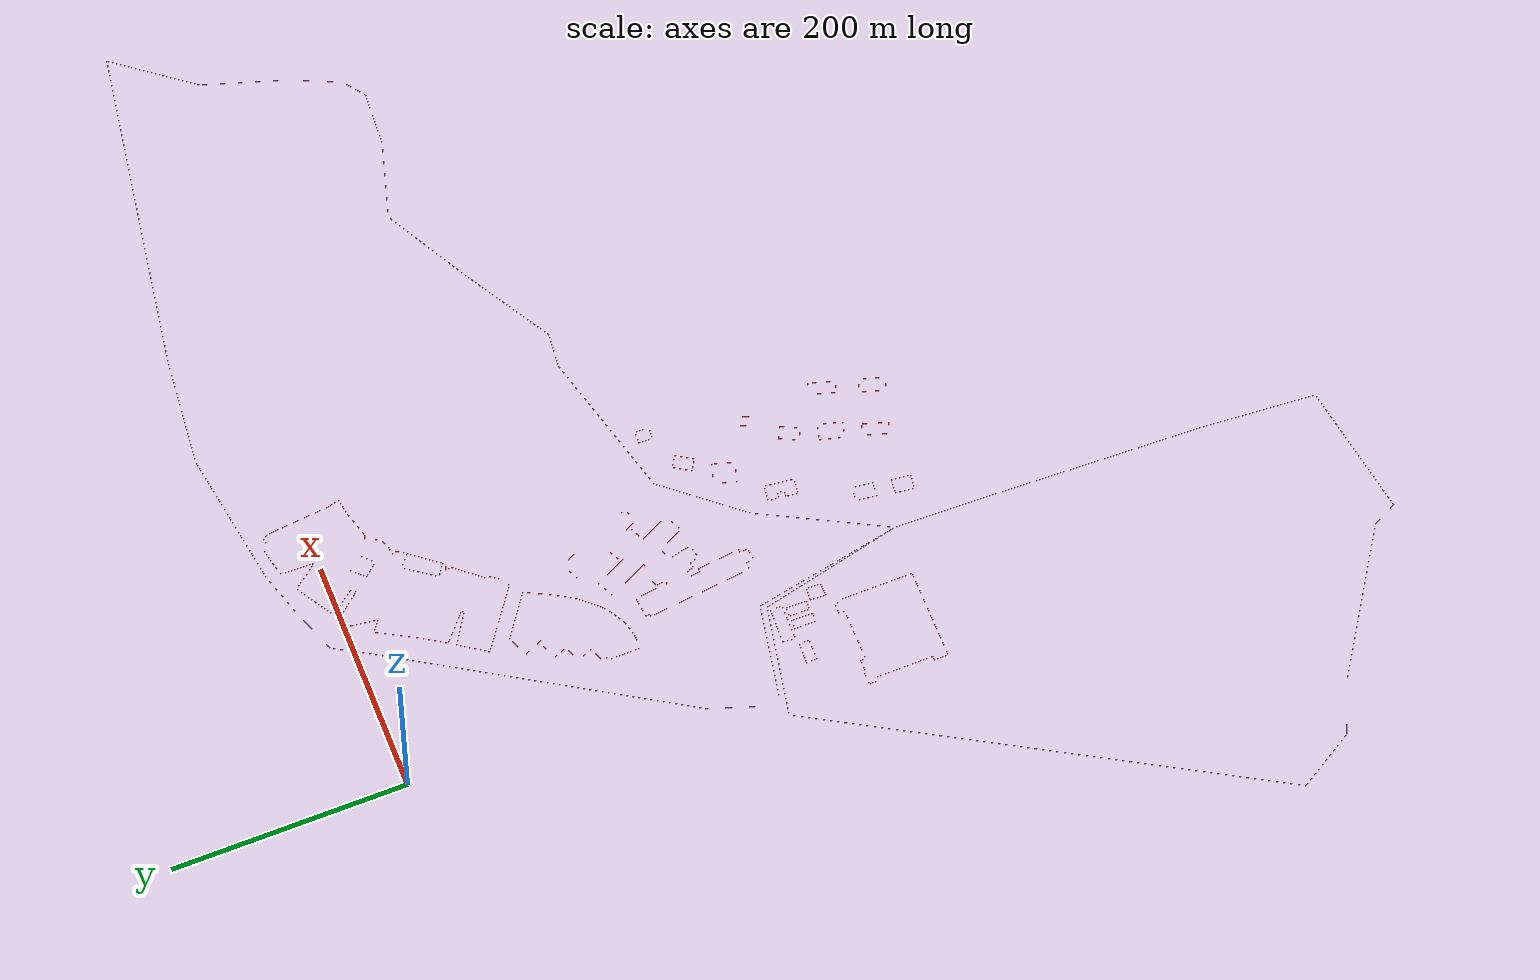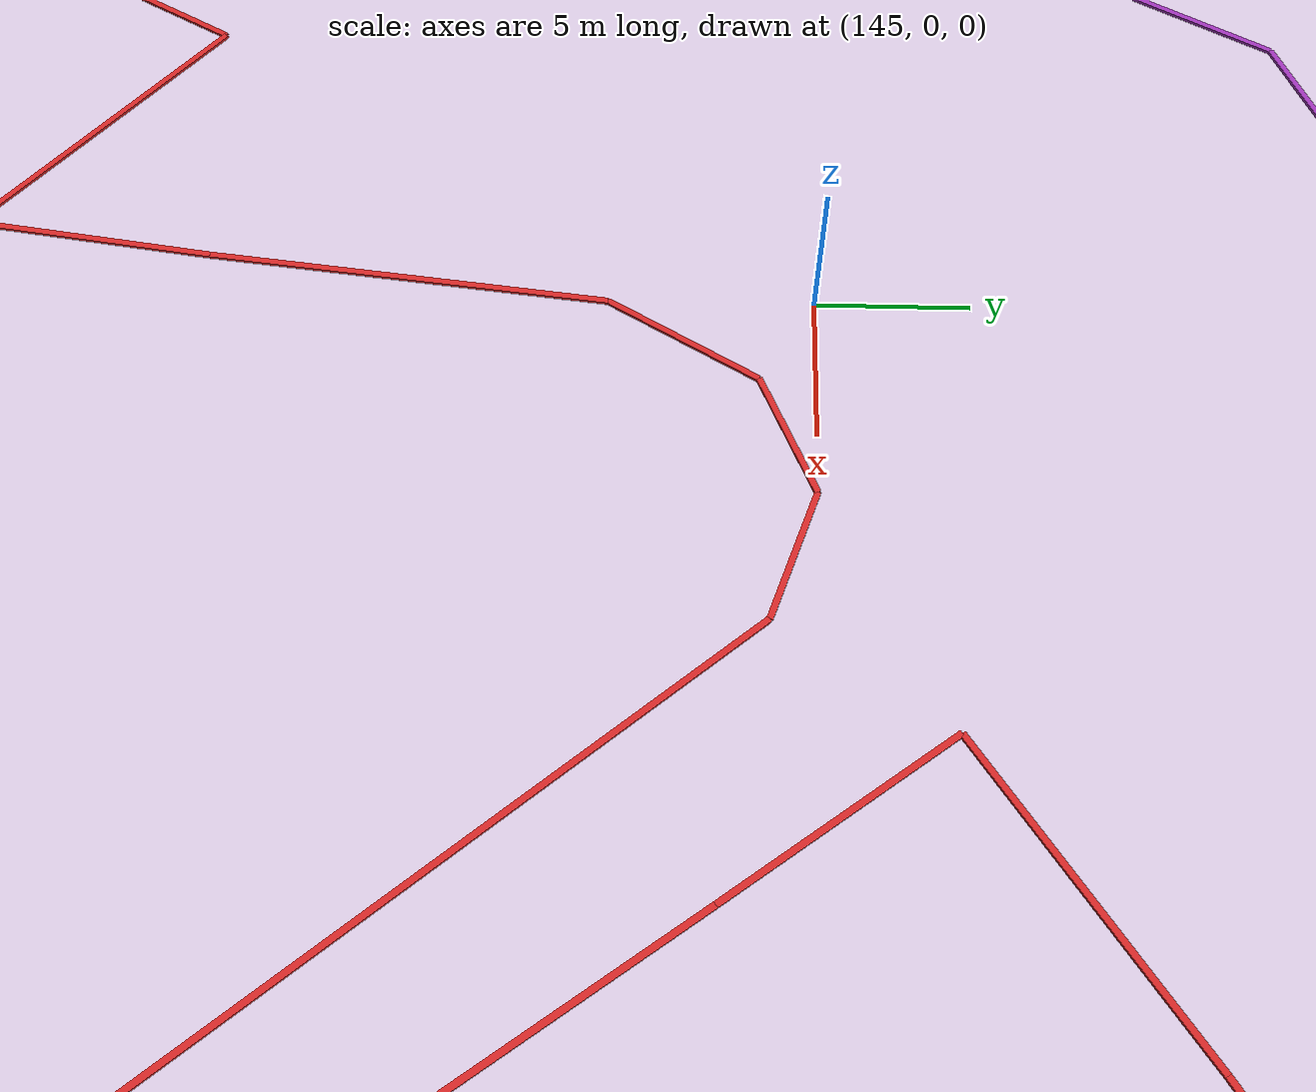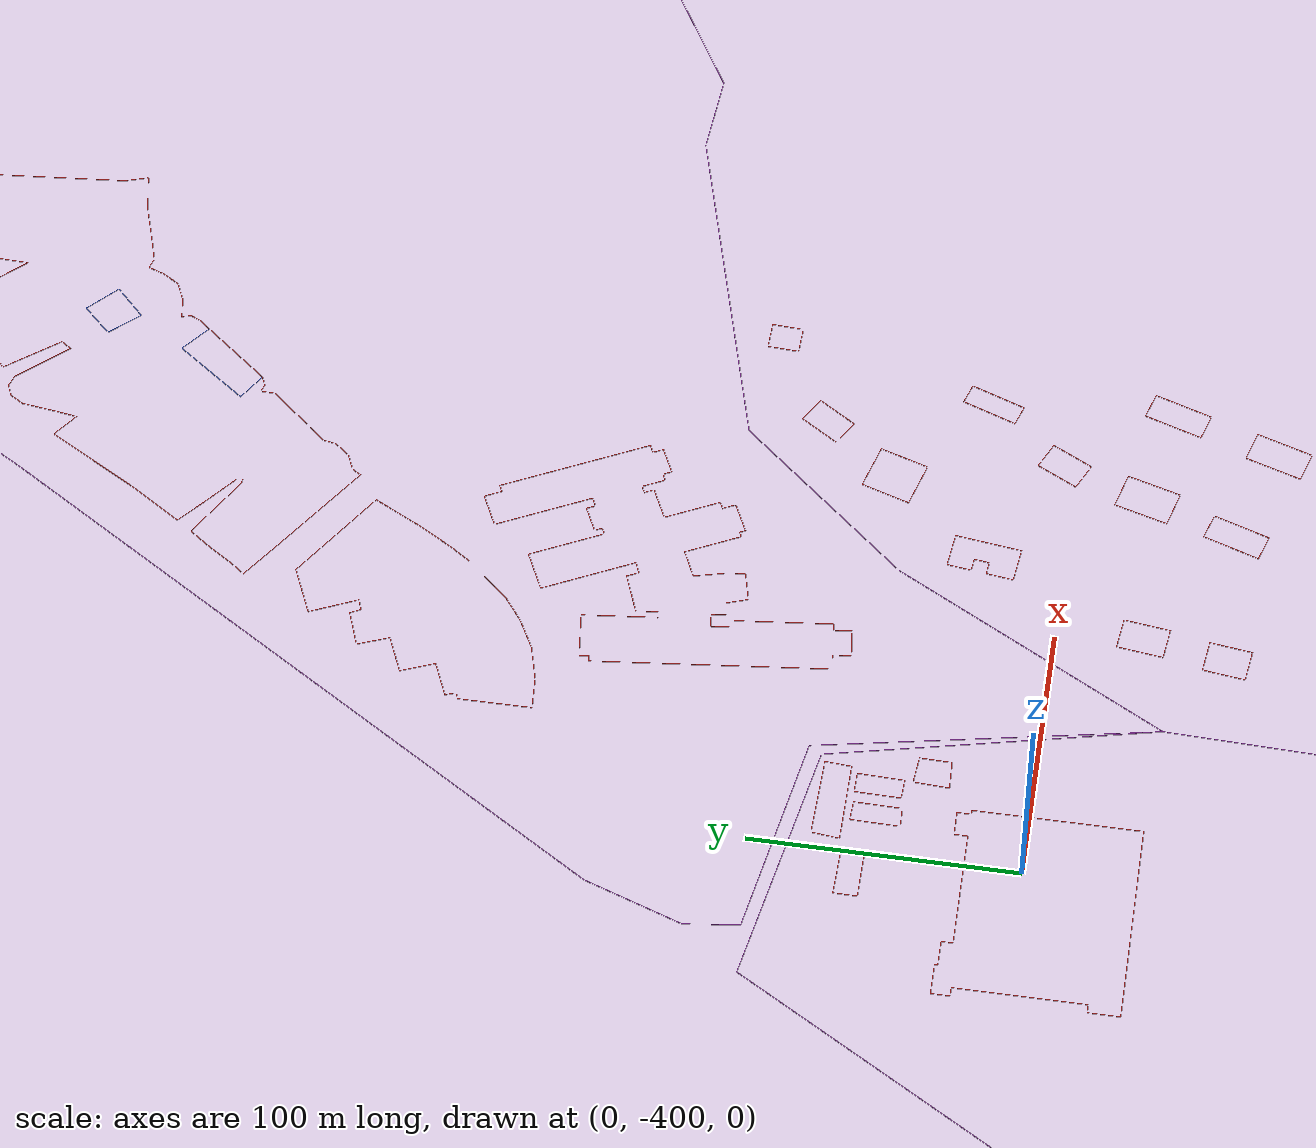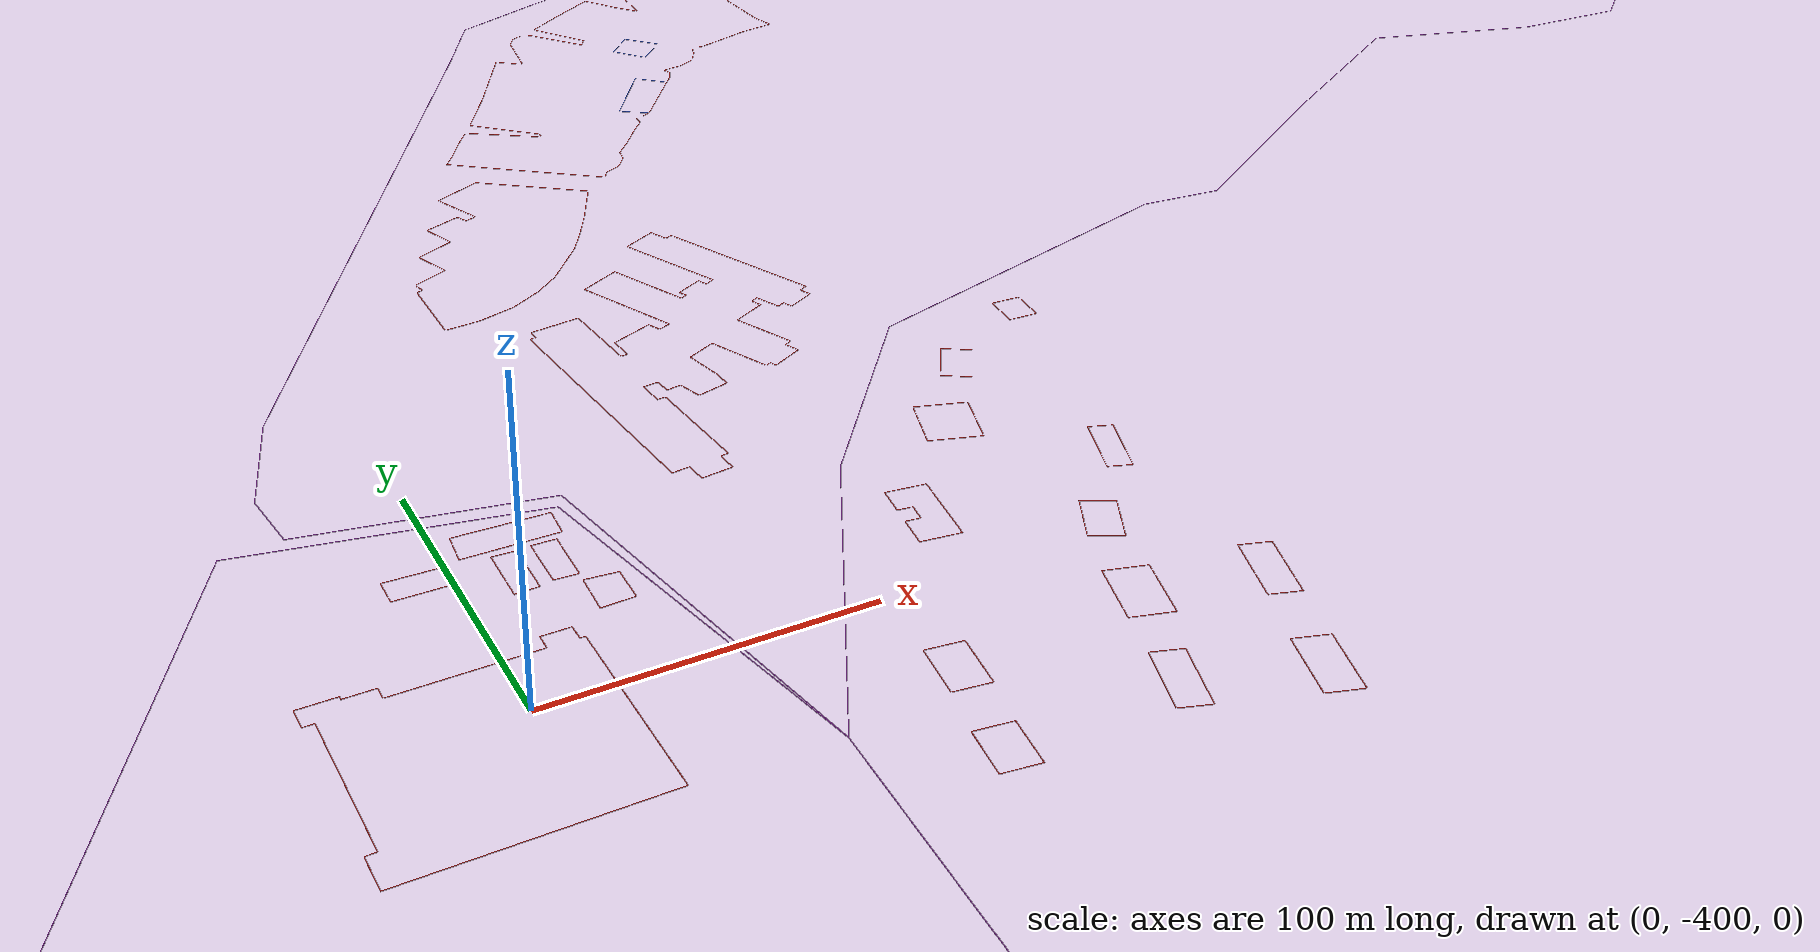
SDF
<sdf version="1.4">
 <world name="default">
  <spherical_coordinates>
   <surface_model>EARTH_WGS84</surface_model>
   <latitude_deg>1.30311</latitude_deg>
   <longitude_deg>103.77207</longitude_deg>
   <elevation>0.0</elevation>
   <heading_deg>0</heading_deg>
  </spherical_coordinates>
  <include><uri>model://sun</uri></include>
  <model name="university_0">
   <static>true</static>
   <pose>295.491620902 -151.413346378 0.0 0 0 0</pose>
   <link name="university_0_0">
    <collision name="university_0_0">
     <geometry><box><size>117.042642465 0.2 0.1</size></box></geometry>
    </collision>
    <visual name="university_0_0">
     <geometry><box><size>117.042642465 0.2 0.1</size></box></geometry>
     <material>
      <script><uri>file://media/materials/scripts/gazebo.material</uri><name>Gazebo/Purple</name></script>
     </material>
    </visual>
    <pose>-202.19879854 -240.386132471 0 0 0 -2.05158336107</pose>
   </link>
   <link name="university_0_1">
    <collision name="university_0_1">
     <geometry><box><size>82.1581091735 0.2 0.1</size></box></geometry>
    </collision>
    <visual name="university_0_1">
     <geometry><box><size>82.1581091735 0.2 0.1</size></box></geometry>
     <material>
      <script><uri>file://media/materials/scripts/gazebo.material</uri><name>Gazebo/Purple</name></script>
     </material>
    </visual>
    <pose>-148.892058081 -156.894748287 0 0 0 -2.26375499913</pose>
   </link>
   <link name="university_0_2">
    <collision name="university_0_2">
     <geometry><box><size>129.938251981 0.2 0.1</size></box></geometry>
    </collision>
    <visual name="university_0_2">
     <geometry><box><size>129.938251981 0.2 0.1</size></box></geometry>
     <material>
      <script><uri>file://media/materials/scripts/gazebo.material</uri><name>Gazebo/Purple</name></script>
     </material>
    </visual>
    <pose>-59.9862051617 -108.137210497 0 0 0 -2.87440755925</pose>
   </link>
   <link name="university_0_3">
    <collision name="university_0_3">
     <geometry><box><size>29.7764563671 0.2 0.1</size></box></geometry>
    </collision>
    <visual name="university_0_3">
     <geometry><box><size>29.7764563671 0.2 0.1</size></box></geometry>
     <material>
      <script><uri>file://media/materials/scripts/gazebo.material</uri><name>Gazebo/Purple</name></script>
     </material>
    </visual>
    <pose>17.5055244999 -92.3237648311 0 0 0 3.05149786161</pose>
   </link>
   <link name="university_0_4">
    <collision name="university_0_4">
     <geometry><box><size>87.2444165234 0.2 0.1</size></box></geometry>
    </collision>
    <visual name="university_0_4">
     <geometry><box><size>87.2444165234 0.2 0.1</size></box></geometry>
     <material>
      <script><uri>file://media/materials/scripts/gazebo.material</uri><name>Gazebo/Purple</name></script>
     </material>
    </visual>
    <pose>69.8116014028 -71.341135291 0 0 0 -2.60441212249</pose>
   </link>
   <link name="university_0_5">
    <collision name="university_0_5">
     <geometry><box><size>81.6554633951 0.2 0.1</size></box></geometry>
    </collision>
    <visual name="university_0_5">
     <geometry><box><size>81.6554633951 0.2 0.1</size></box></geometry>
     <material>
      <script><uri>file://media/materials/scripts/gazebo.material</uri><name>Gazebo/Purple</name></script>
     </material>
    </visual>
    <pose>143.011191091 -29.2480725743 0 0 0 -2.63608504838</pose>
   </link>
   <link name="university_0_6">
    <collision name="university_0_6"><geometry><box><size>67.830235326 0.2 0.1</size></box></geometry></collision>
    <visual name="university_0_6">
     <geometry><box><size>67.830235326 0.2 0.1</size></box></geometry>
     <material>
      <script><uri>file://media/materials/scripts/gazebo.material</uri><name>Gazebo/Purple</name></script>
     </material>
    </visual>
    <pose>211.301548293 -18.9373813023 0 0 0 2.85890495708</pose>
   </link>
   <link name="university_0_7">
    <collision name="university_0_7">
     <geometry><box><size>45.8589411992 0.2 0.1</size></box></geometry>
    </collision>
    <visual name="university_0_7">
     <geometry><box><size>45.8589411992 0.2 0.1</size></box></geometry>
     <material>
      <script><uri>file://media/materials/scripts/gazebo.material</uri><name>Gazebo/Purple</name></script>
     </material>
    </visual>
    <pose>266.765584284 -29.6537456363 0 0 0 3.08678155222</pose>
   </link>
   <link name="university_0_8">
    <collision name="university_0_8">
     <geometry><box><size>22.2726161195 0.2 0.1</size></box></geometry>
    </collision>
    <visual name="university_0_8">
     <geometry><box><size>22.2726161195 0.2 0.1</size></box></geometry>
     <material>
      <script><uri>file://media/materials/scripts/gazebo.material</uri><name>Gazebo/Purple</name></script>
     </material>
    </visual>
    <pose>298.545090921 -24.1954780477 0 0 0 -2.49442244871</pose>
   </link>
   <link name="university_0_9">
    <collision name="university_0_9">
     <geometry><box><size>44.6292755276 0.2 0.1</size></box></geometry>
    </collision>
    <visual name="university_0_9">
     <geometry><box><size>44.6292755276 0.2 0.1</size></box></geometry>
     <material>
      <script><uri>file://media/materials/scripts/gazebo.material</uri><name>Gazebo/Purple</name></script>
     </material>
    </visual>
    <pose>316.525295525 2.89566891227 0 0 0 -1.99063473339</pose>
   </link>
   <link name="university_0_10">
    <collision name="university_0_10">
     <geometry><box><size>73.1124647251 0.2 0.1</size></box></geometry>
    </collision>
    <visual name="university_0_10">
     <geometry><box><size>73.1124647251 0.2 0.1</size></box></geometry>
     <material>
      <script><uri>file://media/materials/scripts/gazebo.material</uri><name>Gazebo/Purple</name></script>
     </material>
    </visual>
    <pose>336.779428977 58.0839987919 0 0 0 -1.88098605295</pose>
   </link>
   <link name="university_0_11">
    <collision name="university_0_11">
     <geometry><box><size>79.9003867261 0.2 0.1</size></box></geometry>
    </collision>
    <visual name="university_0_11">
     <geometry><box><size>79.9003867261 0.2 0.1</size></box></geometry>
     <material>
      <script><uri>file://media/materials/scripts/gazebo.material</uri><name>Gazebo/Purple</name></script>
     </material>
    </visual>
    <pose>372.150520487 124.67238551 0 0 0 -2.22190919371</pose>
   </link>
   <link name="university_0_12">
    <collision name="university_0_12">
     <geometry><box><size>186.156989051 0.2 0.1</size></box></geometry>
    </collision>
    <visual name="university_0_12">
     <geometry><box><size>186.156989051 0.2 0.1</size></box></geometry>
     <material>
      <script><uri>file://media/materials/scripts/gazebo.material</uri><name>Gazebo/Purple</name></script>
     </material>
    </visual>
    <pose>304.58848116 171.973490323 0 0 0 -0.167570622883</pose>
   </link>
   <link name="university_0_13">
    <collision name="university_0_13">
     <geometry><box><size>92.9566688848 0.2 0.1</size></box></geometry>
    </collision>
    <visual name="university_0_13">
     <geometry><box><size>92.9566688848 0.2 0.1</size></box></geometry>
     <material>
      <script><uri>file://media/materials/scripts/gazebo.material</uri><name>Gazebo/Purple</name></script>
     </material>
    </visual>
    <pose>166.968082534 195.140487931 0 0 0 -0.165185268442</pose>
   </link>
   <link name="university_0_14">
    <collision name="university_0_14">
     <geometry><box><size>91.6029316445 0.2 0.1</size></box></geometry>
    </collision>
    <visual name="university_0_14">
     <geometry><box><size>91.6029316445 0.2 0.1</size></box></geometry>
     <material>
      <script><uri>file://media/materials/scripts/gazebo.material</uri><name>Gazebo/Purple</name></script>
     </material>
    </visual>
    <pose>75.5658549739 207.513279951 0 0 0 -0.103458965198</pose>
   </link>
   <link name="university_0_15">
    <collision name="university_0_15">
     <geometry><box><size>79.8771097791 0.2 0.1</size></box></geometry>
    </collision>
    <visual name="university_0_15">
     <geometry><box><size>79.8771097791 0.2 0.1</size></box></geometry>
     <material>
      <script><uri>file://media/materials/scripts/gazebo.material</uri><name>Gazebo/Purple</name></script>
     </material>
    </visual>
    <pose>-9.45934593198 206.134836289 0 0 0 0.153551825656</pose>
   </link>
   <link name="university_0_16">
    <collision name="university_0_16">
     <geometry><box><size>37.1863674417 0.2 0.1</size></box></geometry>
    </collision>
    <visual name="university_0_16">
     <geometry><box><size>37.1863674417 0.2 0.1</size></box></geometry>
     <material>
      <script><uri>file://media/materials/scripts/gazebo.material</uri><name>Gazebo/Purple</name></script>
     </material>
    </visual>
    <pose>-67.3029484319 197.185978969 0 0 0 0.153360209738</pose>
   </link>
   <link name="university_0_17">
    <collision name="university_0_17">
     <geometry><box><size>41.1869283229 0.2 0.1</size></box></geometry>
    </collision>
    <visual name="university_0_17">
     <geometry><box><size>41.1869283229 0.2 0.1</size></box></geometry>
     <material>
      <script><uri>file://media/materials/scripts/gazebo.material</uri><name>Gazebo/Purple</name></script>
     </material>
    </visual>
    <pose>-105.314935384 188.142623233 0 0 0 0.30596683695</pose>
   </link>
   <link name="university_0_18">
    <collision name="university_0_18">
     <geometry><box><size>39.8487653113 0.2 0.1</size></box></geometry>
    </collision>
    <visual name="university_0_18">
     <geometry><box><size>39.8487653113 0.2 0.1</size></box></geometry>
     <material>
      <script><uri>file://media/materials/scripts/gazebo.material</uri><name>Gazebo/Purple</name></script>
     </material>
    </visual>
    <pose>-143.604909776 174.936094513 0 0 0 0.359175158495</pose>
   </link>
   <link name="university_0_19">
    <collision name="university_0_19">
     <geometry><box><size>31.7749621871 0.2 0.1</size></box></geometry>
    </collision>
    <visual name="university_0_19">
     <geometry><box><size>31.7749621871 0.2 0.1</size></box></geometry>
     <material>
      <script><uri>file://media/materials/scripts/gazebo.material</uri><name>Gazebo/Purple</name></script>
     </material>
    </visual>
    <pose>-170.186057714 154.16470744 0 0 0 1.04832678464</pose>
   </link>
   <link name="university_0_20">
    <collision name="university_0_20">
     <geometry><box><size>273.873991607 0.2 0.1</size></box></geometry>
    </collision>
    <visual name="university_0_20">
     <geometry><box><size>273.873991607 0.2 0.1</size></box></geometry>
     <material>
      <script><uri>file://media/materials/scripts/gazebo.material</uri><name>Gazebo/Purple</name></script>
     </material>
    </visual>
    <pose>-249.545823669 23.5666848845 0 0 0 1.02202636426</pose>
   </link>
   <link name="university_0_21">
    <collision name="university_0_21">
     <geometry><box><size>39.6166162149 0.2 0.1</size></box></geometry>
    </collision>
    <visual name="university_0_21">
     <geometry><box><size>39.6166162149 0.2 0.1</size></box></geometry>
     <material>
      <script><uri>file://media/materials/scripts/gazebo.material</uri><name>Gazebo/Purple</name></script>
     </material>
    </visual>
    <pose>-327.354402626 -112.017154721 0 0 0 1.24302247334</pose>
   </link>
   <link name="university_0_22">
    <collision name="university_0_22">
     <geometry><box><size>21.0358579712 0.2 0.1</size></box></geometry>
    </collision>
    <visual name="university_0_22">
     <geometry><box><size>21.0358579712 0.2 0.1</size></box></geometry>
     <material>
      <script><uri>file://media/materials/scripts/gazebo.material</uri><name>Gazebo/Purple</name></script>
     </material>
    </visual>
    <pose>-332.397064014 -141.203840507 0 0 0 1.69800345011</pose>
   </link>
   <link name="university_0_23">
    <collision name="university_0_23">
     <geometry><box><size>78.5098985046 0.2 0.1</size></box></geometry>
    </collision>
    <visual name="university_0_23">
     <geometry><box><size>78.5098985046 0.2 0.1</size></box></geometry>
     <material>
      <script><uri>file://media/materials/scripts/gazebo.material</uri><name>Gazebo/Purple</name></script>
     </material>
    </visual>
    <pose>-292.455827582 -158.740260818 0 0 0 2.95963277124</pose>
   </link>
   <link name="university_0_24">
    <collision name="university_0_24">
     <geometry><box><size>128.797475417 0.2 0.1</size></box></geometry>
    </collision>
    <visual name="university_0_24">
     <geometry><box><size>128.797475417 0.2 0.1</size></box></geometry>
     <material>
      <script><uri>file://media/materials/scripts/gazebo.material</uri><name>Gazebo/Purple</name></script>
     </material>
    </visual>
    <pose>-241.556256135 -229.058349317 0 0 0 1.76285889635</pose>
   </link>
  </model>
  <model name="Stephen Riady Centre">
   <static>true</static>
   <pose>170.84806976 -44.7917697922 0.0 0 0 0</pose>
   <link name="Stephen Riady Centre_0">
    <collision name="Stephen Riady Centre_0">
     <geometry><box><size>52.582127699 0.2 0.1</size></box></geometry>
    </collision>
    <visual name="Stephen Riady Centre_0">
     <geometry><box><size>52.582127699 0.2 0.1</size></box></geometry>
     <material>
      <script><uri>file://media/materials/scripts/gazebo.material</uri><name>Gazebo/Red</name></script>
     </material>
    </visual>
    <pose>76.4272093369 44.6083459957 0 0 0 1.66057978173</pose>
   </link>
   <link name="Stephen Riady Centre_1">
    <collision name="Stephen Riady Centre_1">
     <geometry><box><size>8.8819335641 0.2 0.1</size></box></geometry>
    </collision>
    <visual name="Stephen Riady Centre_1">
     <geometry><box><size>8.8819335641 0.2 0.1</size></box></geometry>
     <material>
      <script><uri>file://media/materials/scripts/gazebo.material</uri><name>Gazebo/Red</name></script>
     </material>
    </visual>
    <pose>80.1022021434 14.1821926169 0 0 0 1.87203752646</pose>
   </link>
   <link name="Stephen Riady Centre_2">
    <collision name="Stephen Riady Centre_2">
     <geometry><box><size>13.8332507366 0.2 0.1</size></box></geometry>
    </collision>
    <visual name="Stephen Riady Centre_2">
     <geometry><box><size>13.8332507366 0.2 0.1</size></box></geometry>
     <material>
      <script><uri>file://media/materials/scripts/gazebo.material</uri><name>Gazebo/Red</name></script>
     </material>
    </visual>
    <pose>74.5869343833 8.86845374804 0 0 0 0.155726463604</pose>
   </link>
   <link name="Stephen Riady Centre_3">
    <collision name="Stephen Riady Centre_3">
     <geometry><box><size>0.777473817926 0.2 0.1</size></box></geometry>
    </collision>
    <visual name="Stephen Riady Centre_3">
     <geometry><box><size>0.777473817926 0.2 0.1</size></box></geometry>
     <material>
      <script><uri>file://media/materials/scripts/gazebo.material</uri><name>Gazebo/Red</name></script>
     </material>
    </visual>
    <pose>67.3815032891 7.68453415647 0 0 0 0.290015946539</pose>
   </link>
   <link name="Stephen Riady Centre_4">
    <collision name="Stephen Riady Centre_4">
     <geometry><box><size>16.9031135344 0.2 0.1</size></box></geometry>
    </collision>
    <visual name="Stephen Riady Centre_4">
     <geometry><box><size>16.9031135344 0.2 0.1</size></box></geometry>
     <material>
      <script><uri>file://media/materials/scripts/gazebo.material</uri><name>Gazebo/Red</name></script>
     </material>
    </visual>
    <pose>58.9140099838 5.14438808646 0 0 0 0.291511516635</pose>
   </link>
   <link name="Stephen Riady Centre_5">
    <collision name="Stephen Riady Centre_5">
     <geometry><box><size>6.19962652546 0.2 0.1</size></box></geometry>
    </collision>
    <visual name="Stephen Riady Centre_5">
     <geometry><box><size>6.19962652546 0.2 0.1</size></box></geometry>
     <material>
      <script><uri>file://media/materials/scripts/gazebo.material</uri><name>Gazebo/Red</name></script>
     </material>
    </visual>
    <pose>47.8334360154 1.88166206609 0 0 0 0.27231987881</pose>
   </link>
   <link name="Stephen Riady Centre_6">
    <collision name="Stephen Riady Centre_6">
     <geometry><box><size>3.96045056819 0.2 0.1</size></box></geometry>
    </collision>
    <visual name="Stephen Riady Centre_6">
     <geometry><box><size>3.96045056819 0.2 0.1</size></box></geometry>
     <material>
      <script><uri>file://media/materials/scripts/gazebo.material</uri><name>Gazebo/Red</name></script>
     </material>
    </visual>
    <pose>42.985337238 1.72047051394 0 0 0 -0.346529182718</pose>
   </link>
   <link name="Stephen Riady Centre_7">
    <collision name="Stephen Riady Centre_7">
     <geometry><box><size>4.62288117889 0.2 0.1</size></box></geometry>
    </collision>
    <visual name="Stephen Riady Centre_7">
     <geometry><box><size>4.62288117889 0.2 0.1</size></box></geometry>
     <material>
      <script><uri>file://media/materials/scripts/gazebo.material</uri><name>Gazebo/Red</name></script>
     </material>
    </visual>
    <pose>40.3833761998 0.203053041209 0 0 0 1.24516505026</pose>
   </link>
   <link name="Stephen Riady Centre_8">
    <collision name="Stephen Riady Centre_8">
     <geometry><box><size>1.64172950359 0.2 0.1</size></box></geometry>
    </collision>
    <visual name="Stephen Riady Centre_8">
     <geometry><box><size>1.64172950359 0.2 0.1</size></box></geometry>
     <material>
      <script><uri>file://media/materials/scripts/gazebo.material</uri><name>Gazebo/Red</name></script>
     </material>
    </visual>
    <pose>39.382622341 -2.76508159663 0 0 0 1.2468263436</pose>
   </link>
   <link name="Stephen Riady Centre_9">
    <collision name="Stephen Riady Centre_9">
     <geometry><box><size>7.19756853176 0.2 0.1</size></box></geometry>
    </collision>
    <visual name="Stephen Riady Centre_9">
     <geometry><box><size>7.19756853176 0.2 0.1</size></box></geometry>
     <material>
      <script><uri>file://media/materials/scripts/gazebo.material</uri><name>Gazebo/Red</name></script>
     </material>
    </visual>
    <pose>37.2865986748 -6.63922008155 0 0 0 1.0358261044</pose>
   </link>
   <link name="Stephen Riady Centre_10">
    <collision name="Stephen Riady Centre_10">
     <geometry><box><size>7.52828290321 0.2 0.1</size></box></geometry>
    </collision>
    <visual name="Stephen Riady Centre_10">
     <geometry><box><size>7.52828290321 0.2 0.1</size></box></geometry>
     <material>
      <script><uri>file://media/materials/scripts/gazebo.material</uri><name>Gazebo/Red</name></script>
     </material>
    </visual>
    <pose>32.0270795262 -11.2970801541 0 0 0 0.427874338963</pose>
   </link>
   <link name="Stephen Riady Centre_11">
    <collision name="Stephen Riady Centre_11">
     <geometry><box><size>7.6531700833 0.2 0.1</size></box></geometry>
    </collision>
    <visual name="Stephen Riady Centre_11">
     <geometry><box><size>7.6531700833 0.2 0.1</size></box></geometry>
     <material>
      <script><uri>file://media/materials/scripts/gazebo.material</uri><name>Gazebo/Red</name></script>
     </material>
    </visual>
    <pose>24.8049694515 -13.3314210603 0 0 0 0.123782783294</pose>
   </link>
   <link name="Stephen Riady Centre_12">
    <collision name="Stephen Riady Centre_12">
     <geometry><box><size>3.61631259084 0.2 0.1</size></box></geometry>
    </collision>
    <visual name="Stephen Riady Centre_12">
     <geometry><box><size>3.61631259084 0.2 0.1</size></box></geometry>
     <material>
      <script><uri>file://media/materials/scripts/gazebo.material</uri><name>Gazebo/Red</name></script>
     </material>
    </visual>
    <pose>21.4802416191 -15.5491852887 0 0 0 1.83522671124</pose>
   </link>
   <link name="Stephen Riady Centre_13">
    <collision name="Stephen Riady Centre_13">
     <geometry><box><size>4.54693772829 0.2 0.1</size></box></geometry>
    </collision>
    <visual name="Stephen Riady Centre_13">
     <geometry><box><size>4.54693772829 0.2 0.1</size></box></geometry>
     <material>
      <script><uri>file://media/materials/scripts/gazebo.material</uri><name>Gazebo/Red</name></script>
     </material>
    </visual>
    <pose>21.0076640308 -19.3621823853 0 0 0 1.14204754342</pose>
   </link>
   <link name="Stephen Riady Centre_14">
    <collision name="Stephen Riady Centre_14">
     <geometry><box><size>4.69191064328 0.2 0.1</size></box></geometry>
    </collision>
    <visual name="Stephen Riady Centre_14">
     <geometry><box><size>4.69191064328 0.2 0.1</size></box></geometry>
     <material>
      <script><uri>file://media/materials/scripts/gazebo.material</uri><name>Gazebo/Red</name></script>
     </material>
    </visual>
    <pose>18.5724960515 -23.2418796205 0 0 0 0.882605730954</pose>
   </link>
   <link name="Stephen Riady Centre_15">
    <collision name="Stephen Riady Centre_15">
     <geometry><box><size>29.7625770592 0.2 0.1</size></box></geometry>
    </collision>
    <visual name="Stephen Riady Centre_15">
     <geometry><box><size>29.7625770592 0.2 0.1</size></box></geometry>
     <material>
      <script><uri>file://media/materials/scripts/gazebo.material</uri><name>Gazebo/Red</name></script>
     </material>
    </visual>
    <pose>7.93670517896 -36.7930299281 0 0 0 0.908939737258</pose>
   </link>
   <link name="Stephen Riady Centre_16">
    <collision name="Stephen Riady Centre_16">
     <geometry><box><size>3.78578624372 0.2 0.1</size></box></geometry>
    </collision>
    <visual name="Stephen Riady Centre_16">
     <geometry><box><size>3.78578624372 0.2 0.1</size></box></geometry>
     <material>
      <script><uri>file://media/materials/scripts/gazebo.material</uri><name>Gazebo/Red</name></script>
     </material>
    </visual>
    <pose>-2.94927446864 -49.2769860156 0 0 0 0.404412677389</pose>
   </link>
   <link name="Stephen Riady Centre_17">
    <collision name="Stephen Riady Centre_17">
     <geometry><box><size>2.9724758863 0.2 0.1</size></box></geometry>
    </collision>
    <visual name="Stephen Riady Centre_17">
     <geometry><box><size>2.9724758863 0.2 0.1</size></box></geometry>
     <material>
      <script><uri>file://media/materials/scripts/gazebo.material</uri><name>Gazebo/Red</name></script>
     </material>
    </visual>
    <pose>-6.08497132211 -49.5104358806 0 0 0 -0.351243628237</pose>
   </link>
   <link name="Stephen Riady Centre_18">
    <collision name="Stephen Riady Centre_18">
     <geometry><box><size>5.46115446366 0.2 0.1</size></box></geometry>
    </collision>
    <visual name="Stephen Riady Centre_18">
     <geometry><box><size>5.46115446366 0.2 0.1</size></box></geometry>
     <material>
      <script><uri>file://media/materials/scripts/gazebo.material</uri><name>Gazebo/Red</name></script>
     </material>
    </visual>
    <pose>-7.56942282424 -51.7282001623 0 0 0 1.53821320065</pose>
   </link>
   <link name="Stephen Riady Centre_19">
    <collision name="Stephen Riady Centre_19">
     <geometry><box><size>8.92728728974 0.2 0.1</size></box></geometry>
    </collision>
    <visual name="Stephen Riady Centre_19">
     <geometry><box><size>8.92728728974 0.2 0.1</size></box></geometry>
     <material>
      <script><uri>file://media/materials/scripts/gazebo.material</uri><name>Gazebo/Red</name></script>
     </material>
    </visual>
    <pose>-10.5550044188 -57.853453631 0 0 0 0.864608953662</pose>
   </link>
   <link name="Stephen Riady Centre_20">
    <collision name="Stephen Riady Centre_20">
     <geometry><box><size>10.0084094707 0.2 0.1</size></box></geometry>
    </collision>
    <visual name="Stephen Riady Centre_20">
     <geometry><box><size>10.0084094707 0.2 0.1</size></box></geometry>
     <material>
      <script><uri>file://media/materials/scripts/gazebo.material</uri><name>Gazebo/Red</name></script>
     </material>
    </visual>
    <pose>-16.5428484279 -65.1848606412 0 0 0 0.904951132512</pose>
   </link>
   <link name="Stephen Riady Centre_21">
    <collision name="Stephen Riady Centre_21">
     <geometry><box><size>5.40956988327 0.2 0.1</size></box></geometry>
    </collision>
    <visual name="Stephen Riady Centre_21">
     <geometry><box><size>5.40956988327 0.2 0.1</size></box></geometry>
     <material>
      <script><uri>file://media/materials/scripts/gazebo.material</uri><name>Gazebo/Red</name></script>
     </material>
    </visual>
    <pose>-21.4354228193 -71.1378077077 0 0 0 0.841977507472</pose>
   </link>
   <link name="Stephen Riady Centre_22">
    <collision name="Stephen Riady Centre_22">
     <geometry><box><size>3.27583571217 0.2 0.1</size></box></geometry>
    </collision>
    <visual name="Stephen Riady Centre_22">
     <geometry><box><size>3.27583571217 0.2 0.1</size></box></geometry>
     <material>
      <script><uri>file://media/materials/scripts/gazebo.material</uri><name>Gazebo/Red</name></script>
     </material>
    </visual>
    <pose>-24.3264895563 -74.3783010275 0 0 0 0.842898283896</pose>
   </link>
   <link name="Stephen Riady Centre_23">
    <collision name="Stephen Riady Centre_23">
     <geometry><box><size>5.08291046242 0.2 0.1</size></box></geometry>
    </collision>
    <visual name="Stephen Riady Centre_23">
     <geometry><box><size>5.08291046242 0.2 0.1</size></box></geometry>
     <material>
      <script><uri>file://media/materials/scripts/gazebo.material</uri><name>Gazebo/Red</name></script>
     </material>
    </visual>
    <pose>-25.8665376721 -78.1023664151 0 0 0 1.3926586346</pose>
   </link>
   <link name="Stephen Riady Centre_24">
    <collision name="Stephen Riady Centre_24">
     <geometry><box><size>6.9020218278 0.2 0.1</size></box></geometry>
    </collision>
    <visual name="Stephen Riady Centre_24">
     <geometry><box><size>6.9020218278 0.2 0.1</size></box></geometry>
     <material>
      <script><uri>file://media/materials/scripts/gazebo.material</uri><name>Gazebo/Red</name></script>
     </material>
    </visual>
    <pose>-28.4073393915 -83.3494080555 0 0 0 0.92008325988</pose>
   </link>
   <link name="Stephen Riady Centre_25">
    <collision name="Stephen Riady Centre_25">
     <geometry><box><size>6.40374886575 0.2 0.1</size></box></geometry>
    </collision>
    <visual name="Stephen Riady Centre_25">
     <geometry><box><size>6.40374886575 0.2 0.1</size></box></geometry>
     <material>
      <script><uri>file://media/materials/scripts/gazebo.material</uri><name>Gazebo/Red</name></script>
     </material>
    </visual>
    <pose>-33.4500274736 -87.3347155606 0 0 0 0.397503939066</pose>
   </link>
   <link name="Stephen Riady Centre_26">
    <collision name="Stephen Riady Centre_26">
     <geometry><box><size>4.042210234 0.2 0.1</size></box></geometry>
    </collision>
    <visual name="Stephen Riady Centre_26">
     <geometry><box><size>4.042210234 0.2 0.1</size></box></geometry>
     <material>
      <script><uri>file://media/materials/scripts/gazebo.material</uri><name>Gazebo/Red</name></script>
     </material>
    </visual>
    <pose>-37.4586031631 -90.297294439 0 0 0 1.02082816618</pose>
   </link>
   <link name="Stephen Riady Centre_27">
    <collision name="Stephen Riady Centre_27">
     <geometry><box><size>1.79920552058 0.2 0.1</size></box></geometry>
    </collision>
    <visual name="Stephen Riady Centre_27">
     <geometry><box><size>1.79920552058 0.2 0.1</size></box></geometry>
     <material>
      <script><uri>file://media/materials/scripts/gazebo.material</uri><name>Gazebo/Red</name></script>
     </material>
    </visual>
    <pose>-39.2432811616 -91.4923310474 0 0 0 -0.627309637321</pose>
   </link>
   <link name="Stephen Riady Centre_28">
    <collision name="Stephen Riady Centre_28">
     <geometry><box><size>43.810374631 0.2 0.1</size></box></geometry>
    </collision>
    <visual name="Stephen Riady Centre_28">
     <geometry><box><size>43.810374631 0.2 0.1</size></box></geometry>
     <material>
      <script><uri>file://media/materials/scripts/gazebo.material</uri><name>Gazebo/Red</name></script>
     </material>
    </visual>
    <pose>-57.707204632 -78.1079378834 0 0 0 -0.627236011428</pose>
   </link>
   <link name="Stephen Riady Centre_29">
    <collision name="Stephen Riady Centre_29">
     <geometry><box><size>14.7343676443 0.2 0.1</size></box></geometry>
    </collision>
    <visual name="Stephen Riady Centre_29">
     <geometry><box><size>14.7343676443 0.2 0.1</size></box></geometry>
     <material>
      <script><uri>file://media/materials/scripts/gazebo.material</uri><name>Gazebo/Red</name></script>
     </material>
    </visual>
    <pose>-81.3583728305 -60.860523378 0 0 0 -0.63854736122</pose>
   </link>
   <link name="Stephen Riady Centre_30">
    <collision name="Stephen Riady Centre_30">
     <geometry><box><size>6.40379953228 0.2 0.1</size></box></geometry>
    </collision>
    <visual name="Stephen Riady Centre_30">
     <geometry><box><size>6.40379953228 0.2 0.1</size></box></geometry>
     <material>
      <script><uri>file://media/materials/scripts/gazebo.material</uri><name>Gazebo/Red</name></script>
     </material>
    </visual>
    <pose>-85.3613927517 -53.9015249424 0 0 0 -2.21094892664</pose>
   </link>
   <link name="Stephen Riady Centre_31">
    <collision name="Stephen Riady Centre_31">
     <geometry><box><size>11.1529544081 0.2 0.1</size></box></geometry>
    </collision>
    <visual name="Stephen Riady Centre_31">
     <geometry><box><size>11.1529544081 0.2 0.1</size></box></geometry>
     <material>
      <script><uri>file://media/materials/scripts/gazebo.material</uri><name>Gazebo/Red</name></script>
     </material>
    </visual>
    <pose>-80.468818423 -46.6201415304 0 0 0 -2.13458409494</pose>
   </link>
   <link name="Stephen Riady Centre_32">
    <collision name="Stephen Riady Centre_32">
     <geometry><box><size>9.61928240129 0.2 0.1</size></box></geometry>
    </collision>
    <visual name="Stephen Riady Centre_32">
     <geometry><box><size>9.61928240129 0.2 0.1</size></box></geometry>
     <material>
      <script><uri>file://media/materials/scripts/gazebo.material</uri><name>Gazebo/Red</name></script>
     </material>
    </visual>
    <pose>-74.6922446792 -37.993647881 0 0 0 -2.19130238826</pose>
   </link>
   <link name="Stephen Riady Centre_33">
    <collision name="Stephen Riady Centre_33">
     <geometry><box><size>27.5843081443 0.2 0.1</size></box></geometry>
    </collision>
    <visual name="Stephen Riady Centre_33">
     <geometry><box><size>27.5843081443 0.2 0.1</size></box></geometry>
     <material>
      <script><uri>file://media/materials/scripts/gazebo.material</uri><name>Gazebo/Red</name></script>
     </material>
    </visual>
    <pose>-60.2591420759 -41.4842595948 0 0 0 2.57495016177</pose>
   </link>
   <link name="Stephen Riady Centre_34">
    <collision name="Stephen Riady Centre_34">
     <geometry><box><size>1.93293279797 0.2 0.1</size></box></geometry>
    </collision>
    <visual name="Stephen Riady Centre_34">
     <geometry><box><size>1.93293279797 0.2 0.1</size></box></geometry>
     <material>
      <script><uri>file://media/materials/scripts/gazebo.material</uri><name>Gazebo/Red</name></script>
     </material>
    </visual>
    <pose>-47.6607545738 -48.9824108204 0 0 0 3.04366677757</pose>
   </link>
   <link name="Stephen Riady Centre_35">
    <collision name="Stephen Riady Centre_35">
     <geometry><box><size>2.13498017384 0.2 0.1</size></box></geometry>
    </collision>
    <visual name="Stephen Riady Centre_35">
     <geometry><box><size>2.13498017384 0.2 0.1</size></box></geometry>
     <material>
      <script><uri>file://media/materials/scripts/gazebo.material</uri><name>Gazebo/Red</name></script>
     </material>
    </visual>
    <pose>-46.854591674 -48.0208236134 0 0 0 -1.42444333123</pose>
   </link>
   <link name="Stephen Riady Centre_36">
    <collision name="Stephen Riady Centre_36">
     <geometry><box><size>15.2212313969 0.2 0.1</size></box></geometry>
    </collision>
    <visual name="Stephen Riady Centre_36">
     <geometry><box><size>15.2212313969 0.2 0.1</size></box></geometry>
     <material>
      <script><uri>file://media/materials/scripts/gazebo.material</uri><name>Gazebo/Red</name></script>
     </material>
    </visual>
    <pose>-52.7312454523 -41.945596886 0 0 0 -0.720144250169</pose>
   </link>
   <link name="Stephen Riady Centre_37">
    <collision name="Stephen Riady Centre_37">
     <geometry><box><size>12.9063757899 0.2 0.1</size></box></geometry>
    </collision>
    <visual name="Stephen Riady Centre_37">
     <geometry><box><size>12.9063757899 0.2 0.1</size></box></geometry>
     <material>
      <script><uri>file://media/materials/scripts/gazebo.material</uri><name>Gazebo/Red</name></script>
     </material>
    </visual>
    <pose>-63.2169297925 -32.5742957187 0 0 0 -0.740177528186</pose>
   </link>
   <link name="Stephen Riady Centre_38">
    <collision name="Stephen Riady Centre_38">
     <geometry><box><size>9.29924116849 0.2 0.1</size></box></geometry>
    </collision>
    <visual name="Stephen Riady Centre_38">
     <geometry><box><size>9.29924116849 0.2 0.1</size></box></geometry>
     <material>
      <script><uri>file://media/materials/scripts/gazebo.material</uri><name>Gazebo/Red</name></script>
     </material>
    </visual>
    <pose>-65.4964279608 -24.2924199829 0 0 0 -2.13470815079</pose>
   </link>
   <link name="Stephen Riady Centre_39">
    <collision name="Stephen Riady Centre_39">
     <geometry><box><size>13.9422156997 0.2 0.1</size></box></geometry>
    </collision>
    <visual name="Stephen Riady Centre_39">
     <geometry><box><size>13.9422156997 0.2 0.1</size></box></geometry>
     <material>
      <script><uri>file://media/materials/scripts/gazebo.material</uri><name>Gazebo/Red</name></script>
     </material>
    </visual>
    <pose>-59.3028727653 -14.4597747656 0 0 0 -2.1317097277</pose>
   </link>
   <link name="Stephen Riady Centre_40">
    <collision name="Stephen Riady Centre_40">
     <geometry><box><size>14.6205849538 0.2 0.1</size></box></geometry>
    </collision>
    <visual name="Stephen Riady Centre_40">
     <geometry><box><size>14.6205849538 0.2 0.1</size></box></geometry>
     <material>
      <script><uri>file://media/materials/scripts/gazebo.material</uri><name>Gazebo/Red</name></script>
     </material>
    </visual>
    <pose>-52.0474061227 -2.16480015573 0 0 0 -2.07741373552</pose>
   </link>
   <link name="Stephen Riady Centre_41">
    <collision name="Stephen Riady Centre_41">
     <geometry><box><size>22.6035984671 0.2 0.1</size></box></geometry>
    </collision>
    <visual name="Stephen Riady Centre_41">
     <geometry><box><size>22.6035984671 0.2 0.1</size></box></geometry>
     <material>
      <script><uri>file://media/materials/scripts/gazebo.material</uri><name>Gazebo/Red</name></script>
     </material>
    </visual>
    <pose>-43.007260741 14.1043626548 0 0 0 -2.07833917615</pose>
   </link>
   <link name="Stephen Riady Centre_42">
    <collision name="Stephen Riady Centre_42">
     <geometry><box><size>11.2817029174 0.2 0.1</size></box></geometry>
    </collision>
    <visual name="Stephen Riady Centre_42">
     <geometry><box><size>11.2817029174 0.2 0.1</size></box></geometry>
     <material>
      <script><uri>file://media/materials/scripts/gazebo.material</uri><name>Gazebo/Red</name></script>
     </material>
    </visual>
    <pose>-33.0831143175 20.4908572591 0 0 0 2.47436566534</pose>
   </link>
   <link name="Stephen Riady Centre_43">
    <collision name="Stephen Riady Centre_43">
     <geometry><box><size>8.1798842767 0.2 0.1</size></box></geometry>
    </collision>
    <visual name="Stephen Riady Centre_43">
     <geometry><box><size>8.1798842767 0.2 0.1</size></box></geometry>
     <material>
      <script><uri>file://media/materials/scripts/gazebo.material</uri><name>Gazebo/Red</name></script>
     </material>
    </visual>
    <pose>-28.0571036734 21.0466881933 0 0 0 -1.71676669868</pose>
   </link>
   <link name="Stephen Riady Centre_44">
    <collision name="Stephen Riady Centre_44">
     <geometry><box><size>13.191551852 0.2 0.1</size></box></geometry>
    </collision>
    <visual name="Stephen Riady Centre_44">
     <geometry><box><size>13.191551852 0.2 0.1</size></box></geometry>
     <material>
      <script><uri>file://media/materials/scripts/gazebo.material</uri><name>Gazebo/Red</name></script>
     </material>
    </visual>
    <pose>-26.667167741 31.6408187524 0 0 0 -1.69162841467</pose>
   </link>
   <link name="Stephen Riady Centre_45">
    <collision name="Stephen Riady Centre_45">
     <geometry><box><size>5.66650794221 0.2 0.1</size></box></geometry>
    </collision>
    <visual name="Stephen Riady Centre_45">
     <geometry><box><size>5.66650794221 0.2 0.1</size></box></geometry>
     <material>
      <script><uri>file://media/materials/scripts/gazebo.material</uri><name>Gazebo/Red</name></script>
     </material>
    </visual>
    <pose>-24.4043513275 40.611924011 0 0 0 -2.11536831513</pose>
   </link>
   <link name="Stephen Riady Centre_46">
    <collision name="Stephen Riady Centre_46">
     <geometry><box><size>4.44428452986 0.2 0.1</size></box></geometry>
    </collision>
    <visual name="Stephen Riady Centre_46">
     <geometry><box><size>4.44428452986 0.2 0.1</size></box></geometry>
     <material>
      <script><uri>file://media/materials/scripts/gazebo.material</uri><name>Gazebo/Red</name></script>
     </material>
    </visual>
    <pose>-20.8905916845 43.9024409094 0 0 0 -2.74073615479</pose>
   </link>
   <link name="Stephen Riady Centre_47">
    <collision name="Stephen Riady Centre_47">
     <geometry><box><size>4.50447847319 0.2 0.1</size></box></geometry>
    </collision>
    <visual name="Stephen Riady Centre_47">
     <geometry><box><size>4.50447847319 0.2 0.1</size></box></geometry>
     <material>
      <script><uri>file://media/materials/scripts/gazebo.material</uri><name>Gazebo/Red</name></script>
     </material>
    </visual>
    <pose>-16.7152221898 44.035840264 0 0 0 2.80977397103</pose>
   </link>
   <link name="Stephen Riady Centre_48">
    <collision name="Stephen Riady Centre_48">
     <geometry><box><size>24.0911057808 0.2 0.1</size></box></geometry>
    </collision>
    <visual name="Stephen Riady Centre_48">
     <geometry><box><size>24.0911057808 0.2 0.1</size></box></geometry>
     <material>
      <script><uri>file://media/materials/scripts/gazebo.material</uri><name>Gazebo/Red</name></script>
     </material>
    </visual>
    <pose>-6.86891107865 34.05312441 0 0 0 2.26613486426</pose>
   </link>
   <link name="Stephen Riady Centre_49">
    <collision name="Stephen Riady Centre_49">
     <geometry><box><size>4.56098893631 0.2 0.1</size></box></geometry>
    </collision>
    <visual name="Stephen Riady Centre_49">
     <geometry><box><size>4.56098893631 0.2 0.1</size></box></geometry>
     <material>
      <script><uri>file://media/materials/scripts/gazebo.material</uri><name>Gazebo/Red</name></script>
     </material>
    </visual>
    <pose>2.08228074723 26.7217201721 0 0 0 -2.14269110024</pose>
   </link>
   <link name="Stephen Riady Centre_50">
    <collision name="Stephen Riady Centre_50">
     <geometry><box><size>16.3092393169 0.2 0.1</size></box></geometry>
    </collision>
    <visual name="Stephen Riady Centre_50">
     <geometry><box><size>16.3092393169 0.2 0.1</size></box></geometry>
     <material>
      <script><uri>file://media/materials/scripts/gazebo.material</uri><name>Gazebo/Red</name></script>
     </material>
    </visual>
    <pose>-1.47595725435 35.2370434586 0 0 0 -0.942578381613</pose>
   </link>
   <link name="Stephen Riady Centre_51">
    <collision name="Stephen Riady Centre_51">
     <geometry><box><size>8.3431123301 0.2 0.1</size></box></geometry>
    </collision>
    <visual name="Stephen Riady Centre_51">
     <geometry><box><size>8.3431123301 0.2 0.1</size></box></geometry>
     <material>
      <script><uri>file://media/materials/scripts/gazebo.material</uri><name>Gazebo/Red</name></script>
     </material>
    </visual>
    <pose>-8.73698618452 45.1975261043 0 0 0 -0.937565644661</pose>
   </link>
   <link name="Stephen Riady Centre_52">
    <collision name="Stephen Riady Centre_52">
     <geometry><box><size>10.6975225923 0.2 0.1</size></box></geometry>
    </collision>
    <visual name="Stephen Riady Centre_52">
     <geometry><box><size>10.6975225923 0.2 0.1</size></box></geometry>
     <material>
      <script><uri>file://media/materials/scripts/gazebo.material</uri><name>Gazebo/Red</name></script>
     </material>
    </visual>
    <pose>-6.75215666781 51.5228773337 0 0 0 -2.55457443483</pose>
   </link>
   <link name="Stephen Riady Centre_53">
    <collision name="Stephen Riady Centre_53">
     <geometry><box><size>8.35495988195 0.2 0.1</size></box></geometry>
    </collision>
    <visual name="Stephen Riady Centre_53">
     <geometry><box><size>8.35495988195 0.2 0.1</size></box></geometry>
     <material>
      <script><uri>file://media/materials/scripts/gazebo.material</uri><name>Gazebo/Red</name></script>
     </material>
    </visual>
    <pose>1.24831846928 56.6921008412 0 0 0 -2.58508456358</pose>
   </link>
   <link name="Stephen Riady Centre_54">
    <collision name="Stephen Riady Centre_54">
     <geometry><box><size>3.52630595853 0.2 0.1</size></box></geometry>
    </collision>
    <visual name="Stephen Riady Centre_54">
     <geometry><box><size>3.52630595853 0.2 0.1</size></box></geometry>
     <material>
      <script><uri>file://media/materials/scripts/gazebo.material</uri><name>Gazebo/Red</name></script>
     </material>
    </visual>
    <pose>6.29100853659 59.8325429369 0 0 0 -2.58344410681</pose>
   </link>
   <link name="Stephen Riady Centre_55">
    <collision name="Stephen Riady Centre_55">
     <geometry><box><size>15.0106984506 0.2 0.1</size></box></geometry>
    </collision>
    <visual name="Stephen Riady Centre_55">
     <geometry><box><size>15.0106984506 0.2 0.1</size></box></geometry>
     <material>
      <script><uri>file://media/materials/scripts/gazebo.material</uri><name>Gazebo/Red</name></script>
     </material>
    </visual>
    <pose>14.2247668761 64.623801144 0 0 0 -2.60179569016</pose>
   </link>
   <link name="Stephen Riady Centre_56">
    <collision name="Stephen Riady Centre_56">
     <geometry><box><size>7.89139762481 0.2 0.1</size></box></geometry>
    </collision>
    <visual name="Stephen Riady Centre_56">
     <geometry><box><size>7.89139762481 0.2 0.1</size></box></geometry>
     <material>
      <script><uri>file://media/materials/scripts/gazebo.material</uri><name>Gazebo/Red</name></script>
     </material>
    </visual>
    <pose>23.0147258684 65.313030407 0 0 0 2.20934967221</pose>
   </link>
   <link name="Stephen Riady Centre_57">
    <collision name="Stephen Riady Centre_57">
     <geometry><box><size>6.58649972806 0.2 0.1</size></box></geometry>
    </collision>
    <visual name="Stephen Riady Centre_57">
     <geometry><box><size>6.58649972806 0.2 0.1</size></box></geometry>
     <material>
      <script><uri>file://media/materials/scripts/gazebo.material</uri><name>Gazebo/Red</name></script>
     </material>
    </visual>
    <pose>27.217893721 59.4212273004 0 0 0 2.16781435535</pose>
   </link>
   <link name="Stephen Riady Centre_58">
    <collision name="Stephen Riady Centre_58">
     <geometry><box><size>11.4910570296 0.2 0.1</size></box></geometry>
    </collision>
    <visual name="Stephen Riady Centre_58">
     <geometry><box><size>11.4910570296 0.2 0.1</size></box></geometry>
     <material>
      <script><uri>file://media/materials/scripts/gazebo.material</uri><name>Gazebo/Red</name></script>
     </material>
    </visual>
    <pose>32.7943190322 52.3232723216 0 0 0 2.27619244791</pose>
   </link>
   <link name="Stephen Riady Centre_59">
    <collision name="Stephen Riady Centre_59">
     <geometry><box><size>11.609914908 0.2 0.1</size></box></geometry>
    </collision>
    <visual name="Stephen Riady Centre_59">
     <geometry><box><size>11.609914908 0.2 0.1</size></box></geometry>
     <material>
      <script><uri>file://media/materials/scripts/gazebo.material</uri><name>Gazebo/Red</name></script>
     </material>
    </visual>
    <pose>36.6750220402 53.7517563689 0 0 0 -1.5976168073</pose>
   </link>
   <link name="Stephen Riady Centre_60">
    <collision name="Stephen Riady Centre_60">
     <geometry><box><size>15.8749883684 0.2 0.1</size></box></geometry>
    </collision>
    <visual name="Stephen Riady Centre_60">
     <geometry><box><size>15.8749883684 0.2 0.1</size></box></geometry>
     <material>
      <script><uri>file://media/materials/scripts/gazebo.material</uri><name>Gazebo/Red</name></script>
     </material>
    </visual>
    <pose>36.8918529765 67.4918846565 0 0 0 -1.57850133507</pose>
   </link>
   <link name="Stephen Riady Centre_61">
    <collision name="Stephen Riady Centre_61">
     <geometry><box><size>8.64815562976 0.2 0.1</size></box></geometry>
    </collision>
    <visual name="Stephen Riady Centre_61">
     <geometry><box><size>8.64815562976 0.2 0.1</size></box></geometry>
     <material>
      <script><uri>file://media/materials/scripts/gazebo.material</uri><name>Gazebo/Red</name></script>
     </material>
    </visual>
    <pose>41.1005817328 76.6519696895 0 0 0 -2.85488611589</pose>
   </link>
   <link name="Stephen Riady Centre_62">
    <collision name="Stephen Riady Centre_62">
     <geometry><box><size>9.41253022224 0.2 0.1</size></box></geometry>
    </collision>
    <visual name="Stephen Riady Centre_62">
     <geometry><box><size>9.41253022224 0.2 0.1</size></box></geometry>
     <material>
      <script><uri>file://media/materials/scripts/gazebo.material</uri><name>Gazebo/Red</name></script>
     </material>
    </visual>
    <pose>49.851622718 78.8530571069 0 0 0 -2.93220236304</pose>
   </link>
   <link name="Stephen Riady Centre_63">
    <collision name="Stephen Riady Centre_63">
     <geometry><box><size>7.29029667786 0.2 0.1</size></box></geometry>
    </collision>
    <visual name="Stephen Riady Centre_63">
     <geometry><box><size>7.29029667786 0.2 0.1</size></box></geometry>
     <material>
      <script><uri>file://media/materials/scripts/gazebo.material</uri><name>Gazebo/Red</name></script>
     </material>
    </visual>
    <pose>58.04668901 80.4538476431 0 0 0 -2.96996830554</pose>
   </link>
   <link name="Stephen Riady Centre_64">
    <collision name="Stephen Riady Centre_64">
     <geometry><box><size>4.57508790871 0.2 0.1</size></box></geometry>
    </collision>
    <visual name="Stephen Riady Centre_64">
     <geometry><box><size>4.57508790871 0.2 0.1</size></box></geometry>
     <material>
      <script><uri>file://media/materials/scripts/gazebo.material</uri><name>Gazebo/Red</name></script>
     </material>
    </visual>
    <pose>62.5167248826 78.9642216646 0 0 0 1.96493165949</pose>
   </link>
   <link name="Stephen Riady Centre_65">
    <collision name="Stephen Riady Centre_65">
     <geometry><box><size>8.54447117052 0.2 0.1</size></box></geometry>
    </collision>
    <visual name="Stephen Riady Centre_65">
     <geometry><box><size>8.54447117052 0.2 0.1</size></box></geometry>
     <material>
      <script><uri>file://media/materials/scripts/gazebo.material</uri><name>Gazebo/Red</name></script>
     </material>
    </visual>
    <pose>67.6150120894 77.5190620584 0 0 0 -2.98482795394</pose>
   </link>
   <link name="Stephen Riady Centre_66">
    <collision name="Stephen Riady Centre_66">
     <geometry><box><size>7.72301815435 0.2 0.1</size></box></geometry>
    </collision>
    <visual name="Stephen Riady Centre_66">
     <geometry><box><size>7.72301815435 0.2 0.1</size></box></geometry>
     <material>
      <script><uri>file://media/materials/scripts/gazebo.material</uri><name>Gazebo/Red</name></script>
     </material>
    </visual>
    <pose>72.9523682542 74.4897859917 0 0 0 1.86439300697</pose>
   </link>
  </model>
  <model name="office_building_453938289">
   <static>true</static>
   <pose>204.009666149 -432.46498562 0.0 0 0 0</pose>
   <link name="office_building_453938289_0">
    <collision name="office_building_453938289_0">
     <geometry><box><size>22.4463066374 0.2 0.1</size></box></geometry>
    </collision>
    <visual name="office_building_453938289_0">
     <geometry><box><size>22.4463066374 0.2 0.1</size></box></geometry>
     <material>
      <script><uri>file://media/materials/scripts/gazebo.material</uri><name>Gazebo/Red</name></script>
     </material>
    </visual>
    <pose>3.19129956346 -3.32274940277 0 0 0 1.27419273407</pose>
   </link>
   <link name="office_building_453938289_1">
    <collision name="office_building_453938289_1">
     <geometry><box><size>10.0561341026 0.2 0.1</size></box></geometry>
    </collision>
    <visual name="office_building_453938289_1">
     <geometry><box><size>10.0561341026 0.2 0.1</size></box></geometry>
     <material>
      <script><uri>file://media/materials/scripts/gazebo.material</uri><name>Gazebo/Red</name></script>
     </material>
    </visual>
    <pose>-4.89811698091 -12.5884554468 0 0 0 -0.296148700477</pose>
   </link>
   <link name="office_building_453938289_2">
    <collision name="office_building_453938289_2">
     <geometry><box><size>22.4569387714 0.2 0.1</size></box></geometry>
    </collision>
    <visual name="office_building_453938289_2">
     <geometry><box><size>22.4569387714 0.2 0.1</size></box></geometry>
     <material>
      <script><uri>file://media/materials/scripts/gazebo.material</uri><name>Gazebo/Red</name></script>
     </material>
    </visual>
    <pose>-6.42706616032 -0.382421287104 0 0 0 -1.86725523866</pose>
   </link>
   <link name="office_building_453938289_3">
    <collision name="office_building_453938289_3">
     <geometry><box><size>10.059383975 0.2 0.1</size></box></geometry>
    </collision>
    <visual name="office_building_453938289_3">
     <geometry><box><size>10.059383975 0.2 0.1</size></box></geometry>
     <material>
      <script><uri>file://media/materials/scripts/gazebo.material</uri><name>Gazebo/Red</name></script>
     </material>
    </visual>
    <pose>1.66235038405 8.88328475691 0 0 0 2.84438689258</pose>
   </link>
  </model>
  <model name="office_building_453938284">
   <static>true</static>
   <pose>197.562491909 -367.835253814 0.0 0 0 0</pose>
   <link name="office_building_453938284_0">
    <collision name="office_building_453938284_0">
     <geometry><box><size>7.86940442761 0.2 0.1</size></box></geometry>
    </collision>
    <visual name="office_building_453938284_0">
     <geometry><box><size>7.86940442761 0.2 0.1</size></box></geometry>
     <material>
      <script><uri>file://media/materials/scripts/gazebo.material</uri><name>Gazebo/Red</name></script>
     </material>
    </visual>
    <pose>-3.48261493448 -7.7949708452 0 0 0 -0.327925626827</pose>
   </link>
   <link name="office_building_453938284_1">
    <collision name="office_building_453938284_1">
     <geometry><box><size>21.2514018576 0.2 0.1</size></box></geometry>
    </collision>
    <visual name="office_building_453938284_1">
     <geometry><box><size>21.2514018576 0.2 0.1</size></box></geometry>
     <material>
      <script><uri>file://media/materials/scripts/gazebo.material</uri><name>Gazebo/Red</name></script>
     </material>
    </visual>
    <pose>-3.78841577536 3.53285338572 0 0 0 -1.89841443322</pose>
   </link>
   <link name="office_building_453938284_2">
    <collision name="office_building_453938284_2">
     <geometry><box><size>7.87993217944 0.2 0.1</size></box></geometry>
    </collision>
    <visual name="office_building_453938284_2">
     <geometry><box><size>7.87993217944 0.2 0.1</size></box></geometry>
     <material>
      <script><uri>file://media/materials/scripts/gazebo.material</uri><name>Gazebo/Red</name></script>
     </material>
    </visual>
    <pose>3.36140652915 12.3261004915 0 0 0 2.81412145582</pose>
   </link>
   <link name="office_building_453938284_3">
    <collision name="office_building_453938284_3">
     <geometry><box><size>21.2549820976 0.2 0.1</size></box></geometry>
    </collision>
    <visual name="office_building_453938284_3">
     <geometry><box><size>21.2549820976 0.2 0.1</size></box></geometry>
     <material>
      <script><uri>file://media/materials/scripts/gazebo.material</uri><name>Gazebo/Red</name></script>
     </material>
    </visual>
    <pose>3.66720737002 0.998276260574 0 0 0 1.24268289935</pose>
   </link>
  </model>
  <model name="Create">
   <static>true</static>
   <pose>112.964578033 -255.127597629 0.0 0 0 0</pose>
   <link name="Create_0">
    <collision name="Create_0"><geometry><box><size>21.8970941722 0.2 0.1</size></box></geometry></collision>
    <visual name="Create_0">
     <geometry><box><size>21.8970941722 0.2 0.1</size></box></geometry>
     <material>
      <script><uri>file://media/materials/scripts/gazebo.material</uri><name>Gazebo/Red</name></script>
     </material>
    </visual>
    <pose>8.57160761581 -15.3618072316 0 0 0 2.02273978336</pose>
   </link>
   <link name="Create_1">
    <collision name="Create_1"><geometry><box><size>2.00403265379 0.2 0.1</size></box></geometry></collision>
    <visual name="Create_1">
     <geometry><box><size>2.00403265379 0.2 0.1</size></box></geometry>
     <material>
      <script><uri>file://media/materials/scripts/gazebo.material</uri><name>Gazebo/Red</name></script>
     </material>
    </visual>
    <pose>14.253677445 -24.772013841 0 0 0 -2.68797134985</pose>
   </link>
   <link name="Create_2">
    <collision name="Create_2"><geometry><box><size>2.31199583182 0.2 0.1</size></box></geometry></collision>
    <visual name="Create_2">
     <geometry><box><size>2.31199583182 0.2 0.1</size></box></geometry>
     <material>
      <script><uri>file://media/materials/scripts/gazebo.material</uri><name>Gazebo/Red</name></script>
     </material>
    </visual>
    <pose>15.6602938698 -25.3723094679 0 0 0 2.02379462315</pose>
   </link>
   <link name="Create_3">
    <collision name="Create_3"><geometry><box><size>11.7907208099 0.2 0.1</size></box></geometry></collision>
    <visual name="Create_3">
     <geometry><box><size>11.7907208099 0.2 0.1</size></box></geometry>
     <material>
      <script><uri>file://media/materials/scripts/gazebo.material</uri><name>Gazebo/Red</name></script>
     </material>
    </visual>
    <pose>21.4702272661 -23.8382113008 0 0 0 -2.68985464426</pose>
   </link>
   <link name="Create_4">
    <collision name="Create_4"><geometry><box><size>5.15599131593 0.2 0.1</size></box></geometry></collision>
    <visual name="Create_4">
     <geometry><box><size>5.15599131593 0.2 0.1</size></box></geometry>
     <material>
      <script><uri>file://media/materials/scripts/gazebo.material</uri><name>Gazebo/Red</name></script>
     </material>
    </visual>
    <pose>25.6455919299 -18.9468980668 0 0 0 -1.11765286606</pose>
   </link>
   <link name="Create_5">
    <collision name="Create_5"><geometry><box><size>2.76502135164 0.2 0.1</size></box></geometry></collision>
    <visual name="Create_5">
     <geometry><box><size>2.76502135164 0.2 0.1</size></box></geometry>
     <material>
      <script><uri>file://media/materials/scripts/gazebo.material</uri><name>Gazebo/Red</name></script>
     </material>
    </visual>
    <pose>25.7623437527 -16.0287874743 0 0 0 -2.69243294559</pose>
   </link>
   <link name="Create_6">
    <collision name="Create_6"><geometry><box><size>21.7082385738 0.2 0.1</size></box></geometry></collision>
    <visual name="Create_6">
     <geometry><box><size>21.7082385738 0.2 0.1</size></box></geometry>
     <material>
      <script><uri>file://media/materials/scripts/gazebo.material</uri><name>Gazebo/Red</name></script>
     </material>
    </visual>
    <pose>22.2708133774 -5.6625504355 0 0 0 -1.11918470141</pose>
   </link>
   <link name="Create_7">
    <collision name="Create_7"><geometry><box><size>12.5565566298 0.2 0.1</size></box></geometry></collision>
    <visual name="Create_7">
     <geometry><box><size>12.5565566298 0.2 0.1</size></box></geometry>
     <material>
      <script><uri>file://media/materials/scripts/gazebo.material</uri><name>Gazebo/Red</name></script>
     </material>
    </visual>
    <pose>23.1826002497 6.84363812588 0 0 0 -2.68992655964</pose>
   </link>
   <link name="Create_8">
    <collision name="Create_8"><geometry><box><size>3.77885253379 0.2 0.1</size></box></geometry></collision>
    <visual name="Create_8">
     <geometry><box><size>3.77885253379 0.2 0.1</size></box></geometry>
     <material>
      <script><uri>file://media/materials/scripts/gazebo.material</uri><name>Gazebo/Red</name></script>
     </material>
    </visual>
    <pose>28.008456156 11.2847286828 0 0 0 -1.12020339139</pose>
   </link>
   <link name="Create_9">
    <collision name="Create_9"><geometry><box><size>2.78988145049 0.2 0.1</size></box></geometry></collision>
    <visual name="Create_9">
     <geometry><box><size>2.78988145049 0.2 0.1</size></box></geometry>
     <material>
      <script><uri>file://media/materials/scripts/gazebo.material</uri><name>Gazebo/Red</name></script>
     </material>
    </visual>
    <pose>28.4421143661 13.5914258955 0 0 0 -2.69230486208</pose>
   </link>
   <link name="Create_10">
    <collision name="Create_10"><geometry><box><size>8.97455253434 0.2 0.1</size></box></geometry></collision>
    <visual name="Create_10">
     <geometry><box><size>8.97455253434 0.2 0.1</size></box></geometry>
     <material>
      <script><uri>file://media/materials/scripts/gazebo.material</uri><name>Gazebo/Red</name></script>
     </material>
    </visual>
    <pose>31.6612105012 10.1619541622 0 0 0 2.0234668612</pose>
   </link>
   <link name="Create_11">
    <collision name="Create_11"><geometry><box><size>2.76986635695 0.2 0.1</size></box></geometry></collision>
    <visual name="Create_11">
     <geometry><box><size>2.76986635695 0.2 0.1</size></box></geometry>
     <material>
      <script><uri>file://media/materials/scripts/gazebo.material</uri><name>Gazebo/Red</name></script>
     </material>
    </visual>
    <pose>34.8691871289 6.73248243592 0 0 0 -2.68881770004</pose>
   </link>
   <link name="Create_12">
    <collision name="Create_12"><geometry><box><size>3.4108492626 0.2 0.1</size></box></geometry></collision>
    <visual name="Create_12">
     <geometry><box><size>3.4108492626 0.2 0.1</size></box></geometry>
     <material>
      <script><uri>file://media/materials/scripts/gazebo.material</uri><name>Gazebo/Red</name></script>
     </material>
    </visual>
    <pose>36.8595771449 5.80424719479 0 0 0 2.02288539092</pose>
   </link>
   <link name="Create_13">
    <collision name="Create_13"><geometry><box><size>10.2590492169 0.2 0.1</size></box></geometry></collision>
    <visual name="Create_13">
     <geometry><box><size>10.2590492169 0.2 0.1</size></box></geometry>
     <material>
      <script><uri>file://media/materials/scripts/gazebo.material</uri><name>Gazebo/Red</name></script>
     </material>
    </visual>
    <pose>42.2191719875 6.51015670991 0 0 0 -2.68967901427</pose>
   </link>
   <link name="Create_14">
    <collision name="Create_14"><geometry><box><size>4.05227690467 0.2 0.1</size></box></geometry></collision>
    <visual name="Create_14">
     <geometry><box><size>4.05227690467 0.2 0.1</size></box></geometry>
     <material>
      <script><uri>file://media/materials/scripts/gazebo.material</uri><name>Gazebo/Red</name></script>
     </material>
    </visual>
    <pose>45.9497581958 10.5732812373 0 0 0 -1.11931540834</pose>
   </link>
   <link name="Create_15">
    <collision name="Create_15"><geometry><box><size>3.19765950304 0.2 0.1</size></box></geometry></collision>
    <visual name="Create_15">
     <geometry><box><size>3.19765950304 0.2 0.1</size></box></geometry>
     <material>
      <script><uri>file://media/materials/scripts/gazebo.material</uri><name>Gazebo/Red</name></script>
     </material>
    </visual>
    <pose>46.505730636 13.0911940073 0 0 0 -2.69204162087</pose>
   </link>
   <link name="Create_16">
    <collision name="Create_16"><geometry><box><size>58.6061526058 0.2 0.1</size></box></geometry></collision>
    <visual name="Create_16">
     <geometry><box><size>58.6061526058 0.2 0.1</size></box></geometry>
     <material>
      <script><uri>file://media/materials/scripts/gazebo.material</uri><name>Gazebo/Red</name></script>
     </material>
    </visual>
    <pose>35.1527077803 40.1490166215 0 0 0 -1.11900791776</pose>
   </link>
   <link name="Create_17">
    <collision name="Create_17"><geometry><box><size>2.75500901032 0.2 0.1</size></box></geometry></collision>
    <visual name="Create_17">
     <geometry><box><size>2.75500901032 0.2 0.1</size></box></geometry>
     <material>
      <script><uri>file://media/materials/scripts/gazebo.material</uri><name>Gazebo/Red</name></script>
     </material>
    </visual>
    <pose>21.1198881983 65.9117519668 0 0 0 0.450911929233</pose>
   </link>
   <link name="Create_18">
    <collision name="Create_18"><geometry><box><size>6.79684179636 0.2 0.1</size></box></geometry></collision>
    <visual name="Create_18">
     <geometry><box><size>6.79684179636 0.2 0.1</size></box></geometry>
     <material>
      <script><uri>file://media/materials/scripts/gazebo.material</uri><name>Gazebo/Red</name></script>
     </material>
    </visual>
    <pose>18.3956108617 68.3685213261 0 0 0 -1.11875016774</pose>
   </link>
   <link name="Create_19">
    <collision name="Create_19"><geometry><box><size>12.9097662137 0.2 0.1</size></box></geometry></collision>
    <visual name="Create_19">
     <geometry><box><size>12.9097662137 0.2 0.1</size></box></geometry>
     <material>
      <script><uri>file://media/materials/scripts/gazebo.material</uri><name>Gazebo/Red</name></script>
     </material>
    </visual>
    <pose>11.1012235072 68.6130818478 0 0 0 0.450835472883</pose>
   </link>
   <link name="Create_20">
    <collision name="Create_20"><geometry><box><size>38.021629747 0.2 0.1</size></box></geometry></collision>
    <visual name="Create_20">
     <geometry><box><size>38.021629747 0.2 0.1</size></box></geometry>
     <material>
      <script><uri>file://media/materials/scripts/gazebo.material</uri><name>Gazebo/Red</name></script>
     </material>
    </visual>
    <pose>13.5920043475 48.6976738974 0 0 0 2.02264691597</pose>
   </link>
   <link name="Create_21">
    <collision name="Create_21"><geometry><box><size>3.53570124826 0.2 0.1</size></box></geometry></collision>
    <visual name="Create_21">
     <geometry><box><size>3.53570124826 0.2 0.1</size></box></geometry>
     <material>
      <script><uri>file://media/materials/scripts/gazebo.material</uri><name>Gazebo/Red</name></script>
     </material>
    </visual>
    <pose>20.3026314 30.8221668655 0 0 0 0.45229525788</pose>
   </link>
   <link name="Create_22">
    <collision name="Create_22"><geometry><box><size>3.4854208494 0.2 0.1</size></box></geometry></collision>
    <visual name="Create_22">
     <geometry><box><size>3.4854208494 0.2 0.1</size></box></geometry>
     <material>
      <script><uri>file://media/materials/scripts/gazebo.material</uri><name>Gazebo/Red</name></script>
     </material>
    </visual>
    <pose>17.9508580687 31.6170027255 0 0 0 -1.11845783531</pose>
   </link>
   <link name="Create_23">
    <collision name="Create_23"><geometry><box><size>10.0601619166 0.2 0.1</size></box></geometry></collision>
    <visual name="Create_23">
     <geometry><box><size>10.0601619166 0.2 0.1</size></box></geometry>
     <material>
      <script><uri>file://media/materials/scripts/gazebo.material</uri><name>Gazebo/Red</name></script>
     </material>
    </visual>
    <pose>12.663539812 30.9889098908 0 0 0 0.451683636351</pose>
   </link>
   <link name="Create_24">
    <collision name="Create_24"><geometry><box><size>2.97827907213 0.2 0.1</size></box></geometry></collision>
    <visual name="Create_24">
     <geometry><box><size>2.97827907213 0.2 0.1</size></box></geometry>
     <material>
      <script><uri>file://media/materials/scripts/gazebo.material</uri><name>Gazebo/Red</name></script>
     </material>
    </visual>
    <pose>8.78839946438 27.4538241893 0 0 0 2.02286093774</pose>
   </link>
   <link name="Create_25">
    <collision name="Create_25"><geometry><box><size>2.55612491321 0.2 0.1</size></box></geometry></collision>
    <visual name="Create_25">
     <geometry><box><size>2.55612491321 0.2 0.1</size></box></geometry>
     <material>
      <script><uri>file://media/materials/scripts/gazebo.material</uri><name>Gazebo/Red</name></script>
     </material>
    </visual>
    <pose>8.28802383931 25.5584414165 0 0 0 0.449929121115</pose>
   </link>
   <link name="Create_26">
    <collision name="Create_26"><geometry><box><size>29.2856501709 0.2 0.1</size></box></geometry></collision>
    <visual name="Create_26">
     <geometry><box><size>29.2856501709 0.2 0.1</size></box></geometry>
     <material>
      <script><uri>file://media/materials/scripts/gazebo.material</uri><name>Gazebo/Red</name></script>
     </material>
    </visual>
    <pose>0.743438313837 38.1757905909 0 0 0 -1.11893017634</pose>
   </link>
   <link name="Create_27">
    <collision name="Create_27"><geometry><box><size>15.3961535564 0.2 0.1</size></box></geometry></collision>
    <visual name="Create_27">
     <geometry><box><size>15.3961535564 0.2 0.1</size></box></geometry>
     <material>
      <script><uri>file://media/materials/scripts/gazebo.material</uri><name>Gazebo/Red</name></script>
     </material>
    </visual>
    <pose>-12.5777216241 47.991749088 0 0 0 0.451273403544</pose>
   </link>
   <link name="Create_28">
    <collision name="Create_28"><geometry><box><size>36.7487781483 0.2 0.1</size></box></geometry></collision>
    <visual name="Create_28">
     <geometry><box><size>36.7487781483 0.2 0.1</size></box></geometry>
     <material>
      <script><uri>file://media/materials/scripts/gazebo.material</uri><name>Gazebo/Red</name></script>
     </material>
    </visual>
    <pose>-11.4824357103 28.1041300273 0 0 0 2.02264067308</pose>
   </link>
   <link name="Create_29">
    <collision name="Create_29"><geometry><box><size>4.52596395074 0.2 0.1</size></box></geometry></collision>
    <visual name="Create_29">
     <geometry><box><size>4.52596395074 0.2 0.1</size></box></geometry>
     <material>
      <script><uri>file://media/materials/scripts/gazebo.material</uri><name>Gazebo/Red</name></script>
     </material>
    </visual>
    <pose>-5.56129173032 10.7344271028 0 0 0 0.379961815455</pose>
   </link>
   <link name="Create_30">
    <collision name="Create_30"><geometry><box><size>4.67926182362 0.2 0.1</size></box></geometry></collision>
    <visual name="Create_30">
     <geometry><box><size>4.67926182362 0.2 0.1</size></box></geometry>
     <material>
      <script><uri>file://media/materials/scripts/gazebo.material</uri><name>Gazebo/Red</name></script>
     </material>
    </visual>
    <pose>-8.66919103216 12.0072765647 0 0 0 -1.12617353116</pose>
   </link>
   <link name="Create_31">
    <collision name="Create_31"><geometry><box><size>5.84204101974 0.2 0.1</size></box></geometry></collision>
    <visual name="Create_31">
     <geometry><box><size>5.84204101974 0.2 0.1</size></box></geometry>
     <material>
      <script><uri>file://media/materials/scripts/gazebo.material</uri><name>Gazebo/Red</name></script>
     </material>
    </visual>
    <pose>-12.4053415037 13.0800264483 0 0 0 0.363808982551</pose>
   </link>
   <link name="Create_32">
    <collision name="Create_32"><geometry><box><size>9.60050321512 0.2 0.1</size></box></geometry></collision>
    <visual name="Create_32">
     <geometry><box><size>9.60050321512 0.2 0.1</size></box></geometry>
     <material>
      <script><uri>file://media/materials/scripts/gazebo.material</uri><name>Gazebo/Red</name></script>
     </material>
    </visual>
    <pose>-19.6218898545 10.334216732 0 0 0 0.363429923924</pose>
   </link>
   <link name="Create_33">
    <collision name="Create_33"><geometry><box><size>8.31104637511 0.2 0.1</size></box></geometry></collision>
    <visual name="Create_33">
     <geometry><box><size>8.31104637511 0.2 0.1</size></box></geometry>
     <material>
      <script><uri>file://media/materials/scripts/gazebo.material</uri><name>Gazebo/Red</name></script>
     </material>
    </visual>
    <pose>-23.6471410118 4.49799123519 0 0 0 1.68207386202</pose>
   </link>
   <link name="Create_34">
    <collision name="Create_34"><geometry><box><size>2.43749642923 0.2 0.1</size></box></geometry></collision>
    <visual name="Create_34">
     <geometry><box><size>2.43749642923 0.2 0.1</size></box></geometry>
     <material>
      <script><uri>file://media/materials/scripts/gazebo.material</uri><name>Gazebo/Red</name></script>
     </material>
    </visual>
    <pose>-24.3977029541 0.240327629006 0 0 0 0.105089608574</pose>
   </link>
   <link name="Create_35">
    <collision name="Create_35"><geometry><box><size>28.2343160329 0.2 0.1</size></box></geometry></collision>
    <visual name="Create_35">
     <geometry><box><size>28.2343160329 0.2 0.1</size></box></geometry>
     <material>
      <script><uri>file://media/materials/scripts/gazebo.material</uri><name>Gazebo/Red</name></script>
     </material>
    </visual>
    <pose>-27.133110112 14.1472086956 0 0 0 -1.46267579046</pose>
   </link>
   <link name="Create_36">
    <collision name="Create_36"><geometry><box><size>17.3925757495 0.2 0.1</size></box></geometry></collision>
    <visual name="Create_36">
     <geometry><box><size>17.3925757495 0.2 0.1</size></box></geometry>
     <material>
      <script><uri>file://media/materials/scripts/gazebo.material</uri><name>Gazebo/Red</name></script>
     </material>
    </visual>
    <pose>-37.3018974694 27.2425710096 0 0 0 0.108229779184</pose>
   </link>
   <link name="Create_37">
    <collision name="Create_37"><geometry><box><size>3.5895930265 0.2 0.1</size></box></geometry></collision>
    <visual name="Create_37">
     <geometry><box><size>3.5895930265 0.2 0.1</size></box></geometry>
     <material>
      <script><uri>file://media/materials/scripts/gazebo.material</uri><name>Gazebo/Red</name></script>
     </material>
    </visual>
    <pose>-45.7527096624 24.5189936749 0 0 0 1.67943029135</pose>
   </link>
   <link name="Create_38">
    <collision name="Create_38"><geometry><box><size>2.16977665831 0.2 0.1</size></box></geometry></collision>
    <visual name="Create_38">
     <geometry><box><size>2.16977665831 0.2 0.1</size></box></geometry>
     <material>
      <script><uri>file://media/materials/scripts/gazebo.material</uri><name>Gazebo/Red</name></script>
     </material>
    </visual>
    <pose>-46.6367077632 22.6180519051 0 0 0 0.107800708113</pose>
   </link>
   <link name="Create_39">
    <collision name="Create_39"><geometry><box><size>89.062313308 0.2 0.1</size></box></geometry></collision>
    <visual name="Create_39">
     <geometry><box><size>89.062313308 0.2 0.1</size></box></geometry>
     <material>
      <script><uri>file://media/materials/scripts/gazebo.material</uri><name>Gazebo/Red</name></script>
     </material>
    </visual>
    <pose>-42.9171935919 -21.7705844302 0 0 0 1.6787530464</pose>
   </link>
   <link name="Create_40">
    <collision name="Create_40"><geometry><box><size>5.93835376865 0.2 0.1</size></box></geometry></collision>
    <visual name="Create_40">
     <geometry><box><size>5.93835376865 0.2 0.1</size></box></geometry>
     <material>
      <script><uri>file://media/materials/scripts/gazebo.material</uri><name>Gazebo/Red</name></script>
     </material>
    </visual>
    <pose>-35.1668637882 -65.7256685426 0 0 0 -3.03468382871</pose>
   </link>
   <link name="Create_41">
    <collision name="Create_41"><geometry><box><size>6.87718975647 0.2 0.1</size></box></geometry></collision>
    <visual name="Create_41">
     <geometry><box><size>6.87718975647 0.2 0.1</size></box></geometry>
     <material>
      <script><uri>file://media/materials/scripts/gazebo.material</uri><name>Gazebo/Red</name></script>
     </material>
    </visual>
    <pose>-31.8421318885 -68.8271999412 0 0 0 1.67934049916</pose>
   </link>
   <link name="Create_42">
    <collision name="Create_42"><geometry><box><size>10.614337739 0.2 0.1</size></box></geometry></collision>
    <visual name="Create_42">
     <geometry><box><size>10.614337739 0.2 0.1</size></box></geometry>
     <material>
      <script><uri>file://media/materials/scripts/gazebo.material</uri><name>Gazebo/Red</name></script>
     </material>
    </visual>
    <pose>-26.193426326 -71.6730464647 0 0 0 -3.03350715389</pose>
   </link>
   <link name="Create_43">
    <collision name="Create_43"><geometry><box><size>6.72006571316 0.2 0.1</size></box></geometry></collision>
    <visual name="Create_43">
     <geometry><box><size>6.72006571316 0.2 0.1</size></box></geometry>
     <material>
      <script><uri>file://media/materials/scripts/gazebo.material</uri><name>Gazebo/Red</name></script>
     </material>
    </visual>
    <pose>-21.2786150863 -67.7599928446 0 0 0 -1.4630331628</pose>
   </link>
   <link name="Create_44">
    <collision name="Create_44"><geometry><box><size>2.70760497003 0.2 0.1</size></box></geometry></collision>
    <visual name="Create_44">
     <geometry><box><size>2.70760497003 0.2 0.1</size></box></geometry>
     <material>
      <script><uri>file://media/materials/scripts/gazebo.material</uri><name>Gazebo/Red</name></script>
     </material>
    </visual>
    <pose>-20.2945440082 -64.269375163 0 0 0 -3.03050931313</pose>
   </link>
   <link name="Create_45">
    <collision name="Create_45"><geometry><box><size>36.5306693546 0.2 0.1</size></box></geometry></collision>
    <visual name="Create_45">
     <geometry><box><size>36.5306693546 0.2 0.1</size></box></geometry>
     <material>
      <script><uri>file://media/materials/scripts/gazebo.material</uri><name>Gazebo/Red</name></script>
     </material>
    </visual>
    <pose>-20.9172552943 -45.9603137278 0 0 0 -1.46283233161</pose>
   </link>
   <link name="Create_46">
    <collision name="Create_46"><geometry><box><size>2.78497505698 0.2 0.1</size></box></geometry></collision>
    <visual name="Create_46">
     <geometry><box><size>2.78497505698 0.2 0.1</size></box></geometry>
     <material>
      <script><uri>file://media/materials/scripts/gazebo.material</uri><name>Gazebo/Red</name></script>
     </material>
    </visual>
    <pose>-24.2698017076 -27.9514037865 0 0 0 0.10798498387</pose>
   </link>
   <link name="Create_47">
    <collision name="Create_47"><geometry><box><size>8.60940315345 0.2 0.1</size></box></geometry></collision>
    <visual name="Create_47">
     <geometry><box><size>8.60940315345 0.2 0.1</size></box></geometry>
     <material>
      <script><uri>file://media/materials/scripts/gazebo.material</uri><name>Gazebo/Red</name></script>
     </material>
    </visual>
    <pose>-26.1156416024 -23.8215837468 0 0 0 -1.46339012368</pose>
   </link>
   <link name="Create_48">
    <collision name="Create_48"><geometry><box><size>5.0664971961 0.2 0.1</size></box></geometry></collision>
    <visual name="Create_48">
     <geometry><box><size>5.0664971961 0.2 0.1</size></box></geometry>
     <material>
      <script><uri>file://media/materials/scripts/gazebo.material</uri><name>Gazebo/Red</name></script>
     </material>
    </visual>
    <pose>-24.0585399893 -19.2693285312 0 0 0 -3.03387051528</pose>
   </link>
   <link name="Create_49">
    <collision name="Create_49"><geometry><box><size>5.57239834225 0.2 0.1</size></box></geometry></collision>
    <visual name="Create_49">
     <geometry><box><size>5.57239834225 0.2 0.1</size></box></geometry>
     <material>
      <script><uri>file://media/materials/scripts/gazebo.material</uri><name>Gazebo/Red</name></script>
     </material>
    </visual>
    <pose>-21.100752486 -21.7483303816 0 0 0 1.72909890915</pose>
   </link>
   <link name="Create_50">
    <collision name="Create_50"><geometry><box><size>4.89742063641 0.2 0.1</size></box></geometry></collision>
    <visual name="Create_50">
     <geometry><box><size>4.89742063641 0.2 0.1</size></box></geometry>
     <material>
      <script><uri>file://media/materials/scripts/gazebo.material</uri><name>Gazebo/Red</name></script>
     </material>
    </visual>
    <pose>-18.2430405323 -24.1161661619 0 0 0 -2.98432163273</pose>
   </link>
   <link name="Create_51">
    <collision name="Create_51"><geometry><box><size>8.3317501144 0.2 0.1</size></box></geometry></collision>
    <visual name="Create_51">
     <geometry><box><size>8.3317501144 0.2 0.1</size></box></geometry>
     <material>
      <script><uri>file://media/materials/scripts/gazebo.material</uri><name>Gazebo/Red</name></script>
     </material>
    </visual>
    <pose>-14.4902081535 -27.6790368594 0 0 0 1.89684585781</pose>
   </link>
   <link name="Create_52">
    <collision name="Create_52"><geometry><box><size>11.0709327905 0.2 0.1</size></box></geometry></collision>
    <visual name="Create_52">
     <geometry><box><size>11.0709327905 0.2 0.1</size></box></geometry>
     <material>
      <script><uri>file://media/materials/scripts/gazebo.material</uri><name>Gazebo/Red</name></script>
     </material>
    </visual>
    <pose>-7.77403191641 -30.3303422526 0 0 0 -2.90544146746</pose>
   </link>
   <link name="Create_53">
    <collision name="Create_53"><geometry><box><size>6.04414586093 0.2 0.1</size></box></geometry></collision>
    <visual name="Create_53">
     <geometry><box><size>6.04414586093 0.2 0.1</size></box></geometry>
     <material>
      <script><uri>file://media/materials/scripts/gazebo.material</uri><name>Gazebo/Red</name></script>
     </material>
    </visual>
    <pose>-2.63127090259 -26.0226496299 0 0 0 -1.49160492837</pose>
   </link>
   <link name="Create_54">
    <collision name="Create_54"><geometry><box><size>13.2869657472 0.2 0.1</size></box></geometry></collision>
    <visual name="Create_54">
     <geometry><box><size>13.2869657472 0.2 0.1</size></box></geometry>
     <material>
      <script><uri>file://media/materials/scripts/gazebo.material</uri><name>Gazebo/Red</name></script>
     </material>
    </visual>
    <pose>-4.47155622025 -16.5624141269 0 0 0 -1.32737948126</pose>
   </link>
   <link name="Create_55">
    <collision name="Create_55"><geometry><box><size>1.0445324527 0.2 0.1</size></box></geometry></collision>
    <visual name="Create_55">
     <geometry><box><size>1.0445324527 0.2 0.1</size></box></geometry>
     <material>
      <script><uri>file://media/materials/scripts/gazebo.material</uri><name>Gazebo/Red</name></script>
     </material>
    </visual>
    <pose>-5.60019119264 -9.89244767621 0 0 0 -2.70184891599</pose>
   </link>
   <link name="Create_56">
    <collision name="Create_56"><geometry><box><size>9.83938483166 0.2 0.1</size></box></geometry></collision>
    <visual name="Create_56">
     <geometry><box><size>9.83938483166 0.2 0.1</size></box></geometry>
     <material>
      <script><uri>file://media/materials/scripts/gazebo.material</uri><name>Gazebo/Red</name></script>
     </material>
    </visual>
    <pose>-0.668698355453 -7.59130426443 0 0 0 -2.70533685063</pose>
   </link>
  </model>
  <model name="office_building_453938282">
   <static>true</static>
   <pose>191.945079586 -471.484302823 0.0 0 0 0</pose>
   <link name="office_building_453938282_0">
    <collision name="office_building_453938282_0">
     <geometry><box><size>21.8817446466 0.2 0.1</size></box></geometry>
    </collision>
    <visual name="office_building_453938282_0">
     <geometry><box><size>21.8817446466 0.2 0.1</size></box></geometry>
     <material>
      <script><uri>file://media/materials/scripts/gazebo.material</uri><name>Gazebo/Red</name></script>
     </material>
    </visual>
    <pose>3.79175278189 -3.41168095876 0 0 0 1.28223884345</pose>
   </link>
   <link name="office_building_453938282_1">
    <collision name="office_building_453938282_1">
     <geometry><box><size>11.5215307308 0.2 0.1</size></box></geometry>
    </collision>
    <visual name="office_building_453938282_1">
     <geometry><box><size>11.5215307308 0.2 0.1</size></box></geometry>
     <material>
      <script><uri>file://media/materials/scripts/gazebo.material</uri><name>Gazebo/Red</name></script>
     </material>
    </visual>
    <pose>-4.84251833073 -12.2549582968 0 0 0 -0.289627749921</pose>
   </link>
   <link name="office_building_453938282_2">
    <collision name="office_building_453938282_2">
     <geometry><box><size>21.874257102 0.2 0.1</size></box></geometry>
    </collision>
    <visual name="office_building_453938282_2">
     <geometry><box><size>21.874257102 0.2 0.1</size></box></geometry>
     <material>
      <script><uri>file://media/materials/scripts/gazebo.material</uri><name>Gazebo/Red</name></script>
     </material>
    </visual>
    <pose>-7.24434925109 -0.126741560281 0 0 0 -1.85998575147</pose>
   </link>
   <link name="office_building_453938282_3">
    <collision name="office_building_453938282_3">
     <geometry><box><size>11.5077019032 0.2 0.1</size></box></geometry>
    </collision>
    <visual name="office_building_453938282_3">
     <geometry><box><size>11.5077019032 0.2 0.1</size></box></geometry>
     <material>
      <script><uri>file://media/materials/scripts/gazebo.material</uri><name>Gazebo/Red</name></script>
     </material>
    </visual>
    <pose>1.38992186152 8.71653577774 0 0 0 2.85261465234</pose>
   </link>
  </model>
  <model name="Create Tower">
   <static>true</static>
   <pose>78.6562306515 -170.22248239 0.0 0 0 0</pose>
   <link name="Create Tower_0">
    <collision name="Create Tower_0">
     <geometry><box><size>42.0427421831 0.2 0.1</size></box></geometry>
    </collision>
    <visual name="Create Tower_0">
     <geometry><box><size>42.0427421831 0.2 0.1</size></box></geometry>
     <material>
      <script><uri>file://media/materials/scripts/gazebo.material</uri><name>Gazebo/Red</name></script>
     </material>
    </visual>
    <pose>26.6342768861 37.9681415945 0 0 0 -0.616929539661</pose>
   </link>
   <link name="Create Tower_1">
    <collision name="Create Tower_1">
     <geometry><box><size>18.7220354538 0.2 0.1</size></box></geometry>
    </collision>
    <visual name="Create Tower_1">
     <geometry><box><size>18.7220354538 0.2 0.1</size></box></geometry>
     <material>
      <script><uri>file://media/materials/scripts/gazebo.material</uri><name>Gazebo/Red</name></script>
     </material>
    </visual>
    <pose>0.909326517713 46.3834051843 0 0 0 0.411737794065</pose>
   </link>
   <link name="Create Tower_2">
    <collision name="Create Tower_2">
     <geometry><box><size>19.2604574241 0.2 0.1</size></box></geometry>
    </collision>
    <visual name="Create Tower_2">
     <geometry><box><size>19.2604574241 0.2 0.1</size></box></geometry>
     <material>
      <script><uri>file://media/materials/scripts/gazebo.material</uri><name>Gazebo/Red</name></script>
     </material>
    </visual>
    <pose>-3.80533241859 33.8160712879 0 0 0 1.98366596041</pose>
   </link>
   <link name="Create Tower_3">
    <collision name="Create Tower_3">
     <geometry><box><size>4.29104543205 0.2 0.1</size></box></geometry>
    </collision>
    <visual name="Create Tower_3">
     <geometry><box><size>4.29104543205 0.2 0.1</size></box></geometry>
     <material>
      <script><uri>file://media/materials/scripts/gazebo.material</uri><name>Gazebo/Red</name></script>
     </material>
    </visual>
    <pose>-1.95949195976 24.2669007578 0 0 0 0.346253617191</pose>
   </link>
   <link name="Create Tower_4">
    <collision name="Create Tower_4">
     <geometry><box><size>4.33570704146 0.2 0.1</size></box></geometry>
    </collision>
    <visual name="Create Tower_4">
     <geometry><box><size>4.33570704146 0.2 0.1</size></box></geometry>
     <material>
      <script><uri>file://media/materials/scripts/gazebo.material</uri><name>Gazebo/Red</name></script>
     </material>
    </visual>
    <pose>-4.92283738393 25.4897267618 0 0 0 -1.11966062676</pose>
   </link>
   <link name="Create Tower_5">
    <collision name="Create Tower_5">
     <geometry><box><size>13.7556983636 0.2 0.1</size></box></geometry>
    </collision>
    <visual name="Create Tower_5">
     <geometry><box><size>13.7556983636 0.2 0.1</size></box></geometry>
     <material>
      <script><uri>file://media/materials/scripts/gazebo.material</uri><name>Gazebo/Red</name></script>
     </material>
    </visual>
    <pose>-12.3395387933 25.111757982 0 0 0 0.345443182512</pose>
   </link>
   <link name="Create Tower_6">
    <collision name="Create Tower_6">
     <geometry><box><size>12.5374941642 0.2 0.1</size></box></geometry>
    </collision>
    <visual name="Create Tower_6">
     <geometry><box><size>12.5374941642 0.2 0.1</size></box></geometry>
     <material>
      <script><uri>file://media/materials/scripts/gazebo.material</uri><name>Gazebo/Red</name></script>
     </material>
    </visual>
    <pose>-16.53714287 16.9410442981 0 0 0 1.94200522276</pose>
   </link>
   <link name="Create Tower_7">
    <collision name="Create Tower_7">
     <geometry><box><size>14.6264084723 0.2 0.1</size></box></geometry>
    </collision>
    <visual name="Create Tower_7">
     <geometry><box><size>14.6264084723 0.2 0.1</size></box></geometry>
     <material>
      <script><uri>file://media/materials/scripts/gazebo.material</uri><name>Gazebo/Red</name></script>
     </material>
    </visual>
    <pose>-20.9738155641 8.19226605383 0 0 0 0.408790728863</pose>
   </link>
   <link name="Create Tower_8">
    <collision name="Create Tower_8">
     <geometry><box><size>13.4887029731 0.2 0.1</size></box></geometry>
    </collision>
    <visual name="Create Tower_8">
     <geometry><box><size>13.4887029731 0.2 0.1</size></box></geometry>
     <material>
      <script><uri>file://media/materials/scripts/gazebo.material</uri><name>Gazebo/Red</name></script>
     </material>
    </visual>
    <pose>-25.1992172619 -0.984501766206 0 0 0 1.94817803062</pose>
   </link>
   <link name="Create Tower_9">
    <collision name="Create Tower_9">
     <geometry><box><size>13.6745337207 0.2 0.1</size></box></geometry>
    </collision>
    <visual name="Create Tower_9">
     <geometry><box><size>13.6745337207 0.2 0.1</size></box></geometry>
     <material>
      <script><uri>file://media/materials/scripts/gazebo.material</uri><name>Gazebo/Red</name></script>
     </material>
    </visual>
    <pose>-28.985398929 -9.97784567544 0 0 0 0.409709192072</pose>
   </link>
   <link name="Create Tower_10">
    <collision name="Create Tower_10">
     <geometry><box><size>4.2010247482 0.2 0.1</size></box></geometry>
    </collision>
    <visual name="Create Tower_10">
     <geometry><box><size>4.2010247482 0.2 0.1</size></box></geometry>
     <material>
      <script><uri>file://media/materials/scripts/gazebo.material</uri><name>Gazebo/Red</name></script>
     </material>
    </visual>
    <pose>-34.6007396551 -14.6968523554 0 0 0 1.8884402488</pose>
   </link>
   <link name="Create Tower_11">
    <collision name="Create Tower_11">
     <geometry><box><size>2.48600923432 0.2 0.1</size></box></geometry>
    </collision>
    <visual name="Create Tower_11">
     <geometry><box><size>2.48600923432 0.2 0.1</size></box></geometry>
     <material>
      <script><uri>file://media/materials/scripts/gazebo.material</uri><name>Gazebo/Red</name></script>
     </material>
    </visual>
    <pose>-35.1011152025 -17.1480663389 0 0 0 0.375435400355</pose>
   </link>
   <link name="Create Tower_12">
    <collision name="Create Tower_12">
     <geometry><box><size>27.4035484094 0.2 0.1</size></box></geometry>
    </collision>
    <visual name="Create Tower_12">
     <geometry><box><size>27.4035484094 0.2 0.1</size></box></geometry>
     <material>
      <script><uri>file://media/materials/scripts/gazebo.material</uri><name>Gazebo/Red</name></script>
     </material>
    </visual>
    <pose>-36.1352178558 -31.3050764968 0 0 0 1.57972406872</pose>
   </link>
   <link name="Create Tower_13">
    <collision name="Create Tower_13">
     <geometry><box><size>12.2783644588 0.2 0.1</size></box></geometry>
    </collision>
    <visual name="Create Tower_13">
     <geometry><box><size>12.2783644588 0.2 0.1</size></box></geometry>
     <material>
      <script><uri>file://media/materials/scripts/gazebo.material</uri><name>Gazebo/Red</name></script>
     </material>
    </visual>
    <pose>-29.8860534161 -44.6172184341 0 0 0 -3.07817261555</pose>
   </link>
   <link name="Create Tower_14">
    <collision name="Create Tower_14">
     <geometry><box><size>13.4658885639 0.2 0.1</size></box></geometry>
    </collision>
    <visual name="Create Tower_14">
     <geometry><box><size>13.4658885639 0.2 0.1</size></box></geometry>
     <material>
      <script><uri>file://media/materials/scripts/gazebo.material</uri><name>Gazebo/Red</name></script>
     </material>
    </visual>
    <pose>-17.2431918407 -42.5328435536 0 0 0 -2.88706315742</pose>
   </link>
   <link name="Create Tower_15">
    <collision name="Create Tower_15">
     <geometry><box><size>12.6629065103 0.2 0.1</size></box></geometry>
    </collision>
    <visual name="Create Tower_15">
     <geometry><box><size>12.6629065103 0.2 0.1</size></box></geometry>
     <material>
      <script><uri>file://media/materials/scripts/gazebo.material</uri><name>Gazebo/Red</name></script>
     </material>
    </visual>
    <pose>-5.16742634331 -37.8082734549 0 0 0 -2.64270436267</pose>
   </link>
   <link name="Create Tower_16">
    <collision name="Create Tower_16">
     <geometry><box><size>10.8573338913 0.2 0.1</size></box></geometry>
    </collision>
    <visual name="Create Tower_16">
     <geometry><box><size>10.8573338913 0.2 0.1</size></box></geometry>
     <material>
      <script><uri>file://media/materials/scripts/gazebo.material</uri><name>Gazebo/Red</name></script>
     </material>
    </visual>
    <pose>4.68443951475 -31.4551214566 0 0 0 -2.48265005396</pose>
   </link>
   <link name="Create Tower_17">
    <collision name="Create Tower_17">
     <geometry><box><size>9.83232927854 0.2 0.1</size></box></geometry>
    </collision>
    <visual name="Create Tower_17">
     <geometry><box><size>9.83232927854 0.2 0.1</size></box></geometry>
     <material>
      <script><uri>file://media/materials/scripts/gazebo.material</uri><name>Gazebo/Red</name></script>
     </material>
    </visual>
    <pose>12.2178908327 -24.4349747263 0 0 0 -2.29071135558</pose>
   </link>
   <link name="Create Tower_18">
    <collision name="Create Tower_18">
     <geometry><box><size>10.6807301913 0.2 0.1</size></box></geometry>
    </collision>
    <visual name="Create Tower_18">
     <geometry><box><size>10.6807301913 0.2 0.1</size></box></geometry>
     <material>
      <script><uri>file://media/materials/scripts/gazebo.material</uri><name>Gazebo/Red</name></script>
     </material>
    </visual>
    <pose>18.950738375 -16.6978073864 0 0 0 -2.28338881415</pose>
   </link>
   <link name="Create Tower_19">
    <collision name="Create Tower_19">
     <geometry><box><size>8.28251692443 0.2 0.1</size></box></geometry>
    </collision>
    <visual name="Create Tower_19">
     <geometry><box><size>8.28251692443 0.2 0.1</size></box></geometry>
     <material>
      <script><uri>file://media/materials/scripts/gazebo.material</uri><name>Gazebo/Red</name></script>
     </material>
    </visual>
    <pose>24.7050709099 -9.18853157797 0 0 0 -2.14886503733</pose>
   </link>
   <link name="Create Tower_20">
    <collision name="Create Tower_20">
     <geometry><box><size>8.32262286262 0.2 0.1</size></box></geometry>
    </collision>
    <visual name="Create Tower_20">
     <geometry><box><size>8.32262286262 0.2 0.1</size></box></geometry>
     <material>
      <script><uri>file://media/materials/scripts/gazebo.material</uri><name>Gazebo/Red</name></script>
     </material>
    </visual>
    <pose>29.0805868448 -2.13503806321 0 0 0 -2.10331035394</pose>
   </link>
   <link name="Create Tower_21">
    <collision name="Create Tower_21">
     <geometry><box><size>8.67841581902 0.2 0.1</size></box></geometry>
    </collision>
    <visual name="Create Tower_21">
     <geometry><box><size>8.67841581902 0.2 0.1</size></box></geometry>
     <material>
      <script><uri>file://media/materials/scripts/gazebo.material</uri><name>Gazebo/Red</name></script>
     </material>
    </visual>
    <pose>33.2948701215 5.24639520168 0 0 0 -2.07638648697</pose>
   </link>
   <link name="Create Tower_22">
    <collision name="Create Tower_22">
     <geometry><box><size>8.13881603924 0.2 0.1</size></box></geometry>
    </collision>
    <visual name="Create Tower_22">
     <geometry><box><size>8.13881603924 0.2 0.1</size></box></geometry>
     <material>
      <script><uri>file://media/materials/scripts/gazebo.material</uri><name>Gazebo/Red</name></script>
     </material>
    </visual>
    <pose>37.2033675053 12.6889694464 0 0 0 -2.03088121221</pose>
   </link>
   <link name="Create Tower_23">
    <collision name="Create Tower_23">
     <geometry><box><size>10.6048074378 0.2 0.1</size></box></geometry>
    </collision>
    <visual name="Create Tower_23">
     <geometry><box><size>10.6048074378 0.2 0.1</size></box></geometry>
     <material>
      <script><uri>file://media/materials/scripts/gazebo.material</uri><name>Gazebo/Red</name></script>
     </material>
    </visual>
    <pose>41.3954116661 21.0708973385 0 0 0 -2.0373604132</pose>
   </link>
  </model>
  <model name="Boarding House">
   <static>true</static>
   <pose>-7.13628671864 -337.745063312 0.0 0 0 0</pose>
   <link name="Boarding House_0">
    <collision name="Boarding House_0">
     <geometry><box><size>8.50305447965 0.2 0.1</size></box></geometry>
    </collision>
    <visual name="Boarding House_0">
     <geometry><box><size>8.50305447965 0.2 0.1</size></box></geometry>
     <material>
      <script><uri>file://media/materials/scripts/gazebo.material</uri><name>Gazebo/Red</name></script>
     </material>
    </visual>
    <pose>6.9974979592 -1.01160368657 0 0 0 1.5223935269</pose>
   </link>
   <link name="Boarding House_1">
    <collision name="Boarding House_1">
     <geometry><box><size>17.3920376652 0.2 0.1</size></box></geometry>
    </collision>
    <visual name="Boarding House_1">
     <geometry><box><size>17.3920376652 0.2 0.1</size></box></geometry>
     <material>
      <script><uri>file://media/materials/scripts/gazebo.material</uri><name>Gazebo/Red</name></script>
     </material>
    </visual>
    <pose>-1.90365090918 -5.15811268397 0 0 0 -0.0115042432983</pose>
   </link>
   <link name="Boarding House_2">
    <collision name="Boarding House_2">
     <geometry><box><size>8.90441070119 0.2 0.1</size></box></geometry>
    </collision>
    <visual name="Boarding House_2">
     <geometry><box><size>8.90441070119 0.2 0.1</size></box></geometry>
     <material>
      <script><uri>file://media/materials/scripts/gazebo.material</uri><name>Gazebo/Red</name></script>
     </material>
    </visual>
    <pose>-10.5990996778 -0.605868423691 0 0 0 -1.57079511877</pose>
   </link>
   <link name="Boarding House_3">
    <collision name="Boarding House_3">
     <geometry><box><size>17.8128040673 0.2 0.1</size></box></geometry>
    </collision>
    <visual name="Boarding House_3">
     <geometry><box><size>17.8128040673 0.2 0.1</size></box></geometry>
     <material>
      <script><uri>file://media/materials/scripts/gazebo.material</uri><name>Gazebo/Red</name></script>
     </material>
    </visual>
    <pose>-1.69795080946 3.54064057371 0 0 0 3.1072626956</pose>
   </link>
  </model>
  <model name="office_building_453938264">
   <static>true</static>
   <pose>105.793408467 -430.69092592 0.0 0 0 0</pose>
   <link name="office_building_453938264_0">
    <collision name="office_building_453938264_0">
     <geometry><box><size>17.4882056911 0.2 0.1</size></box></geometry>
    </collision>
    <visual name="office_building_453938264_0">
     <geometry><box><size>17.4882056911 0.2 0.1</size></box></geometry>
     <material>
      <script><uri>file://media/materials/scripts/gazebo.material</uri><name>Gazebo/Red</name></script>
     </material>
    </visual>
    <pose>4.50673393735 -2.30113184477 0 0 0 1.45161606891</pose>
   </link>
   <link name="office_building_453938264_1">
    <collision name="office_building_453938264_1">
     <geometry><box><size>11.8709146059 0.2 0.1</size></box></geometry>
    </collision>
    <visual name="office_building_453938264_1">
     <geometry><box><size>11.8709146059 0.2 0.1</size></box></geometry>
     <material>
      <script><uri>file://media/materials/scripts/gazebo.material</uri><name>Gazebo/Red</name></script>
     </material>
    </visual>
    <pose>-2.42625743034 -10.2773122029 0 0 0 -0.11921075444</pose>
   </link>
   <link name="office_building_453938264_2">
    <collision name="office_building_453938264_2">
     <geometry><box><size>17.4882064169 0.2 0.1</size></box></geometry>
    </collision>
    <visual name="office_building_453938264_2">
     <geometry><box><size>17.4882064169 0.2 0.1</size></box></geometry>
     <material>
      <script><uri>file://media/materials/scripts/gazebo.material</uri><name>Gazebo/Red</name></script>
     </material>
    </visual>
    <pose>-7.27993047559 -0.889340226449 0 0 0 -1.68997658479</pose>
   </link>
   <link name="office_building_453938264_3">
    <collision name="office_building_453938264_3">
     <geometry><box><size>11.8709146039 0.2 0.1</size></box></geometry>
    </collision>
    <visual name="office_building_453938264_3">
     <geometry><box><size>11.8709146039 0.2 0.1</size></box></geometry>
     <material>
      <script><uri>file://media/materials/scripts/gazebo.material</uri><name>Gazebo/Red</name></script>
     </material>
    </visual>
    <pose>-0.346939107906 7.08684013171 0 0 0 3.02238183801</pose>
   </link>
  </model>
  <model name="office_building_453938262">
   <static>true</static>
   <pose>216.71460779 -283.444608361 0.0 0 0 0</pose>
   <link name="office_building_453938262_0">
    <collision name="office_building_453938262_0">
     <geometry><box><size>11.6952378623 0.2 0.1</size></box></geometry>
    </collision>
    <visual name="office_building_453938262_0">
     <geometry><box><size>11.6952378623 0.2 0.1</size></box></geometry>
     <material>
      <script><uri>file://media/materials/scripts/gazebo.material</uri><name>Gazebo/Red</name></script>
     </material>
    </visual>
    <pose>3.94630931737 -1.34621723523 0 0 0 1.52609622307</pose>
   </link>
   <link name="office_building_453938262_1">
    <collision name="office_building_453938262_1">
     <geometry><box><size>10.0063088764 0.2 0.1</size></box></geometry>
    </collision>
    <visual name="office_building_453938262_1">
     <geometry><box><size>10.0063088764 0.2 0.1</size></box></geometry>
     <material>
      <script><uri>file://media/materials/scripts/gazebo.material</uri><name>Gazebo/Red</name></script>
     </material>
    </visual>
    <pose>-1.31320500223 -6.96566809816 0 0 0 -0.0444519988152</pose>
   </link>
   <link name="office_building_453938262_2">
    <collision name="office_building_453938262_2">
     <geometry><box><size>11.6952382793 0.2 0.1</size></box></geometry>
    </collision>
    <visual name="office_building_453938262_2">
     <geometry><box><size>11.6952382793 0.2 0.1</size></box></geometry>
     <material>
      <script><uri>file://media/materials/scripts/gazebo.material</uri><name>Gazebo/Red</name></script>
     </material>
    </visual>
    <pose>-6.05011504332 -0.901563068289 0 0 0 -1.61549643054</pose>
   </link>
   <link name="office_building_453938262_3">
    <collision name="office_building_453938262_3">
     <geometry><box><size>10.0063088761 0.2 0.1</size></box></geometry>
    </collision>
    <visual name="office_building_453938262_3">
     <geometry><box><size>10.0063088761 0.2 0.1</size></box></geometry>
     <material>
      <script><uri>file://media/materials/scripts/gazebo.material</uri><name>Gazebo/Red</name></script>
     </material>
    </visual>
    <pose>-0.790600723727 4.71788779464 0 0 0 3.0971406131</pose>
   </link>
  </model>
  <model name="restaurant_0">
   <static>true</static>
   <pose>192.529569696 -32.8651436003 0.0 0 0 0</pose>
   <link name="restaurant_0_0">
    <collision name="restaurant_0_0">
     <geometry><box><size>14.7577871966 0.2 0.1</size></box></geometry>
    </collision>
    <visual name="restaurant_0_0">
     <geometry><box><size>14.7577871966 0.2 0.1</size></box></geometry>
     <material>
      <script><uri>file://media/materials/scripts/gazebo.material</uri><name>Gazebo/Blue</name></script>
     </material>
    </visual>
    <pose>2.96779200698 5.1403205071 0 0 0 -0.799652104168</pose>
   </link>
   <link name="restaurant_0_1">
    <collision name="restaurant_0_1">
     <geometry><box><size>13.8085559566 0.2 0.1</size></box></geometry>
    </collision>
    <visual name="restaurant_0_1">
     <geometry><box><size>13.8085559566 0.2 0.1</size></box></geometry>
     <material>
      <script><uri>file://media/materials/scripts/gazebo.material</uri><name>Gazebo/Blue</name></script>
     </material>
    </visual>
    <pose>-6.94523573851 5.44046780058 0 0 0 0.808043839673</pose>
   </link>
   <link name="restaurant_0_2">
    <collision name="restaurant_0_2">
     <geometry><box><size>14.4805074495 0.2 0.1</size></box></geometry>
    </collision>
    <visual name="restaurant_0_2">
     <geometry><box><size>14.4805074495 0.2 0.1</size></box></geometry>
     <material>
      <script><uri>file://media/materials/scripts/gazebo.material</uri><name>Gazebo/Blue</name></script>
     </material>
    </visual>
    <pose>-7.02307095115 -5.06472804051 0 0 0 2.27588651522</pose>
   </link>
   <link name="restaurant_0_3">
    <collision name="restaurant_0_3">
     <geometry><box><size>14.7563197821 0.2 0.1</size></box></geometry>
    </collision>
    <visual name="restaurant_0_3">
     <geometry><box><size>14.7563197821 0.2 0.1</size></box></geometry>
     <material>
      <script><uri>file://media/materials/scripts/gazebo.material</uri><name>Gazebo/Blue</name></script>
     </material>
    </visual>
    <pose>2.88995679434 -5.36487533399 0 0 0 -2.35685679603</pose>
   </link>
  </model>
  <model name="office_building_453938287">
   <static>true</static>
   <pose>182.900252881 -304.646240568 0.0 0 0 0</pose>
   <link name="office_building_453938287_0">
    <collision name="office_building_453938287_0">
     <geometry><box><size>16.2584274088 0.2 0.1</size></box></geometry>
    </collision>
    <visual name="office_building_453938287_0">
     <geometry><box><size>16.2584274088 0.2 0.1</size></box></geometry>
     <material>
      <script><uri>file://media/materials/scripts/gazebo.material</uri><name>Gazebo/Red</name></script>
     </material>
    </visual>
    <pose>2.76208592152 -3.60066685535 0 0 0 1.02099798032</pose>
   </link>
   <link name="office_building_453938287_1">
    <collision name="office_building_453938287_1">
     <geometry><box><size>10.5911018078 0.2 0.1</size></box></geometry>
    </collision>
    <visual name="office_building_453938287_1">
     <geometry><box><size>10.5911018078 0.2 0.1</size></box></geometry>
     <material>
      <script><uri>file://media/materials/scripts/gazebo.material</uri><name>Gazebo/Red</name></script>
     </material>
    </visual>
    <pose>-6.00006975875 -7.76384675625 0 0 0 -0.550025249856</pose>
   </link>
   <link name="office_building_453938287_2">
    <collision name="office_building_453938287_2">
     <geometry><box><size>16.2584277899 0.2 0.1</size></box></geometry>
    </collision>
    <visual name="office_building_453938287_2">
     <geometry><box><size>16.2584277899 0.2 0.1</size></box></geometry>
     <material>
      <script><uri>file://media/materials/scripts/gazebo.material</uri><name>Gazebo/Red</name></script>
     </material>
    </visual>
    <pose>-6.2669481662 1.93539492288 0 0 0 -2.12059467869</pose>
   </link>
   <link name="office_building_453938287_3">
    <collision name="office_building_453938287_3">
     <geometry><box><size>10.5911017197 0.2 0.1</size></box></geometry>
    </collision>
    <visual name="office_building_453938287_3">
     <geometry><box><size>10.5911017197 0.2 0.1</size></box></geometry>
     <material>
      <script><uri>file://media/materials/scripts/gazebo.material</uri><name>Gazebo/Red</name></script>
     </material>
    </visual>
    <pose>2.49520751407 6.09857482378 0 0 0 2.59156736775</pose>
   </link>
  </model>
  <model name="office_building_241883364">
   <static>true</static>
   <pose>29.431283315 -342.965381965 0.0 0 0 0</pose>
   <link name="office_building_241883364_0">
    <collision name="office_building_241883364_0">
     <geometry><box><size>17.3909944551 0.2 0.1</size></box></geometry>
    </collision>
    <visual name="office_building_241883364_0">
     <geometry><box><size>17.3909944551 0.2 0.1</size></box></geometry>
     <material>
      <script><uri>file://media/materials/scripts/gazebo.material</uri><name>Gazebo/Red</name></script>
     </material>
    </visual>
    <pose>2.99336971915 -1.86091777291 0 0 0 1.54777776508</pose>
   </link>
   <link name="office_building_241883364_1">
    <collision name="office_building_241883364_1">
     <geometry><box><size>7.49411182347 0.2 0.1</size></box></geometry>
    </collision>
    <visual name="office_building_241883364_1">
     <geometry><box><size>7.49411182347 0.2 0.1</size></box></geometry>
     <material>
      <script><uri>file://media/materials/scripts/gazebo.material</uri><name>Gazebo/Red</name></script>
     </material>
    </visual>
    <pose>-0.948479981054 -10.3540170657 0 0 0 -0.0534258332332</pose>
   </link>
   <link name="office_building_241883364_2">
    <collision name="office_building_241883364_2">
     <geometry><box><size>17.1985695021 0.2 0.1</size></box></geometry>
    </collision>
    <visual name="office_building_241883364_2">
     <geometry><box><size>17.1985695021 0.2 0.1</size></box></geometry>
     <material>
      <script><uri>file://media/materials/scripts/gazebo.material</uri><name>Gazebo/Red</name></script>
     </material>
    </visual>
    <pose>-4.59012466086 -1.55522016887 0 0 0 -1.58243300559</pose>
   </link>
   <link name="office_building_241883364_3">
    <collision name="office_building_241883364_3">
     <geometry><box><size>7.68647196899 0.2 0.1</size></box></geometry>
    </collision>
    <visual name="office_building_241883364_3">
     <geometry><box><size>7.68647196899 0.2 0.1</size></box></geometry>
     <material>
      <script><uri>file://media/materials/scripts/gazebo.material</uri><name>Gazebo/Red</name></script>
     </material>
    </visual>
    <pose>-0.648274960655 6.93787912394 0 0 0 3.11411150642</pose>
   </link>
  </model>
  <model name="office_building_241883365">
   <static>true</static>
   <pose>17.6201587578 -343.410061078 0.0 0 0 0</pose>
   <link name="office_building_241883365_0">
    <collision name="office_building_241883365_0">
     <geometry><box><size>17.7988277503 0.2 0.1</size></box></geometry>
    </collision>
    <visual name="office_building_241883365_0">
     <geometry><box><size>17.7988277503 0.2 0.1</size></box></geometry>
     <material>
      <script><uri>file://media/materials/scripts/gazebo.material</uri><name>Gazebo/Red</name></script>
     </material>
    </visual>
    <pose>2.97335458197 -1.822009712 0 0 0 1.55955215112</pose>
   </link>
   <link name="office_building_241883365_1">
    <collision name="office_building_241883365_1">
     <geometry><box><size>7.48609331339 0.2 0.1</size></box></geometry>
    </collision>
    <visual name="office_building_241883365_1">
     <geometry><box><size>7.48609331339 0.2 0.1</size></box></geometry>
     <material>
      <script><uri>file://media/materials/scripts/gazebo.material</uri><name>Gazebo/Red</name></script>
     </material>
    </visual>
    <pose>-0.868419039436 -10.8209152889 0 0 0 0.0267338901144</pose>
   </link>
   <link name="office_building_241883365_2">
    <collision name="office_building_241883365_2">
     <geometry><box><size>18.4102047526 0.2 0.1</size></box></geometry>
    </collision>
    <visual name="office_building_241883365_2">
     <geometry><box><size>18.4102047526 0.2 0.1</size></box></geometry>
     <material>
      <script><uri>file://media/materials/scripts/gazebo.material</uri><name>Gazebo/Red</name></script>
     </material>
    </visual>
    <pose>-4.51006410517 -1.71641108102 0 0 0 -1.58166704371</pose>
   </link>
   <link name="office_building_241883365_3">
    <collision name="office_building_241883365_3">
     <geometry><box><size>7.49471369098 0.2 0.1</size></box></geometry>
    </collision>
    <visual name="office_building_241883365_3">
     <geometry><box><size>7.49471369098 0.2 0.1</size></box></geometry>
     <material>
      <script><uri>file://media/materials/scripts/gazebo.material</uri><name>Gazebo/Red</name></script>
     </material>
    </visual>
    <pose>-0.668290483764 7.28249449588 0 0 0 3.08668561168</pose>
   </link>
  </model>
  <model name="office_building_241883363">
   <static>true</static>
   <pose>23.5623964563 -327.473273152 0.0 0 0 0</pose>
   <link name="office_building_241883363_0">
    <collision name="office_building_241883363_0">
     <geometry><box><size>9.9237670088 0.2 0.1</size></box></geometry>
    </collision>
    <visual name="office_building_241883363_0">
     <geometry><box><size>9.9237670088 0.2 0.1</size></box></geometry>
     <material>
      <script><uri>file://media/materials/scripts/gazebo.material</uri><name>Gazebo/Red</name></script>
     </material>
    </visual>
    <pose>11.9923743355 -1.27283842455 0 0 0 1.50913141428</pose>
   </link>
   <link name="office_building_241883363_1">
    <collision name="office_building_241883363_1">
     <geometry><box><size>30.3366158083 0.2 0.1</size></box></geometry>
    </collision>
    <visual name="office_building_241883363_1">
     <geometry><box><size>30.3366158083 0.2 0.1</size></box></geometry>
     <material>
      <script><uri>file://media/materials/scripts/gazebo.material</uri><name>Gazebo/Red</name></script>
     </material>
    </visual>
    <pose>-3.48039413885 -6.02520995647 0 0 0 -0.0131911108349</pose>
   </link>
   <link name="office_building_241883363_2">
    <collision name="office_building_241883363_2">
     <geometry><box><size>10.564888171 0.2 0.1</size></box></geometry>
    </collision>
    <visual name="office_building_241883363_2">
     <geometry><box><size>10.564888171 0.2 0.1</size></box></geometry>
     <material>
      <script><uri>file://media/materials/scripts/gazebo.material</uri><name>Gazebo/Red</name></script>
     </material>
    </visual>
    <pose>-18.1414516207 -0.56696864319 0 0 0 -1.66671924531</pose>
   </link>
   <link name="office_building_241883363_3">
    <collision name="office_building_241883363_3">
     <geometry><box><size>29.9507631622 0.2 0.1</size></box></geometry>
    </collision>
    <visual name="office_building_241883363_3">
     <geometry><box><size>29.9507631622 0.2 0.1</size></box></geometry>
     <material>
      <script><uri>file://media/materials/scripts/gazebo.material</uri><name>Gazebo/Red</name></script>
     </material>
    </visual>
    <pose>-2.66868314631 4.18540288873 0 0 0 3.10781154683</pose>
   </link>
  </model>
  <model name="office_building_453938296">
   <static>true</static>
   <pose>176.12636937 -393.943752008 0.0 0 0 0</pose>
   <link name="office_building_453938296_0">
    <collision name="office_building_453938296_0">
     <geometry><box><size>16.6012113789 0.2 0.1</size></box></geometry>
    </collision>
    <visual name="office_building_453938296_0">
     <geometry><box><size>16.6012113789 0.2 0.1</size></box></geometry>
     <material>
      <script><uri>file://media/materials/scripts/gazebo.material</uri><name>Gazebo/Red</name></script>
     </material>
    </visual>
    <pose>3.12569417177 -3.38055666251 0 0 0 1.11513375843</pose>
   </link>
   <link name="office_building_453938296_1">
    <collision name="office_building_453938296_1">
     <geometry><box><size>10.7360435787 0.2 0.1</size></box></geometry>
    </collision>
    <visual name="office_building_453938296_1">
     <geometry><box><size>10.7360435787 0.2 0.1</size></box></geometry>
     <material>
      <script><uri>file://media/materials/scripts/gazebo.material</uri><name>Gazebo/Red</name></script>
     </material>
    </visual>
    <pose>-5.34735206117 -8.47197598878 0 0 0 -0.455669856881</pose>
   </link>
   <link name="office_building_453938296_2">
    <collision name="office_building_453938296_2">
     <geometry><box><size>16.6012118397 0.2 0.1</size></box></geometry>
    </collision>
    <visual name="office_building_453938296_2">
     <geometry><box><size>16.6012118397 0.2 0.1</size></box></geometry>
     <material>
      <script><uri>file://media/materials/scripts/gazebo.material</uri><name>Gazebo/Red</name></script>
     </material>
    </visual>
    <pose>-6.51491263976 1.34398897098 0 0 0 -2.02645889845</pose>
   </link>
   <link name="office_building_453938296_3">
    <collision name="office_building_453938296_3">
     <geometry><box><size>10.736043524 0.2 0.1</size></box></geometry>
    </collision>
    <visual name="office_building_453938296_3">
     <geometry><box><size>10.736043524 0.2 0.1</size></box></geometry>
     <material>
      <script><uri>file://media/materials/scripts/gazebo.material</uri><name>Gazebo/Red</name></script>
     </material>
    </visual>
    <pose>1.95813359319 6.43540829725 0 0 0 2.68592275378</pose>
   </link>
  </model>
  <model name="college_0">
   <static>true</static>
   <pose>-24.9781248399 -601.099268359 0.0 0 0 0</pose>
   <link name="college_0_0">
    <collision name="college_0_0"><geometry><box><size>95.0972648215 0.2 0.1</size></box></geometry></collision>
    <visual name="college_0_0">
     <geometry><box><size>95.0972648215 0.2 0.1</size></box></geometry>
     <material>
      <script><uri>file://media/materials/scripts/gazebo.material</uri><name>Gazebo/Purple</name></script>
     </material>
    </visual>
    <pose>16.9555861925 287.855229839 0 0 0 -0.188380649238</pose>
   </link>
   <link name="college_0_1">
    <collision name="college_0_1"><geometry><box><size>415.578385111 0.2 0.1</size></box></geometry></collision>
    <visual name="college_0_1">
     <geometry><box><size>415.578385111 0.2 0.1</size></box></geometry>
     <material>
      <script><uri>file://media/materials/scripts/gazebo.material</uri><name>Gazebo/Purple</name></script>
     </material>
    </visual>
    <pose>-133.09610586 116.492247952 0 0 0 1.05025315986</pose>
   </link>
   <link name="college_0_2">
    <collision name="college_0_2"><geometry><box><size>55.4272845406 0.2 0.1</size></box></geometry></collision>
    <visual name="college_0_2">
     <geometry><box><size>55.4272845406 0.2 0.1</size></box></geometry>
     <material>
      <script><uri>file://media/materials/scripts/gazebo.material</uri><name>Gazebo/Purple</name></script>
     </material>
    </visual>
    <pose>-221.984960412 -87.4201215814 0 0 0 2.11951994528</pose>
   </link>
   <link name="college_0_3">
    <collision name="college_0_3"><geometry><box><size>48.3689499822 0.2 0.1</size></box></geometry></collision>
    <visual name="college_0_3">
     <geometry><box><size>48.3689499822 0.2 0.1</size></box></geometry>
     <material>
      <script><uri>file://media/materials/scripts/gazebo.material</uri><name>Gazebo/Purple</name></script>
     </material>
    </visual>
    <pose>-185.3461491 -120.697649732 0 0 0 2.73193792228</pose>
   </link>
   <link name="college_0_4">
    <collision name="college_0_4"><geometry><box><size>137.276990369 0.2 0.1</size></box></geometry></collision>
    <visual name="college_0_4">
     <geometry><box><size>137.276990369 0.2 0.1</size></box></geometry>
     <material>
      <script><uri>file://media/materials/scripts/gazebo.material</uri><name>Gazebo/Purple</name></script>
     </material>
    </visual>
    <pose>-105.213399347 -167.114891958 0 0 0 2.57599556131</pose>
   </link>
   <link name="college_0_5">
    <collision name="college_0_5"><geometry><box><size>22.587104298 0.2 0.1</size></box></geometry></collision>
    <visual name="college_0_5">
     <geometry><box><size>22.587104298 0.2 0.1</size></box></geometry>
     <material>
      <script><uri>file://media/materials/scripts/gazebo.material</uri><name>Gazebo/Purple</name></script>
     </material>
    </visual>
    <pose>-42.1546261198 -213.971277986 0 0 0 2.04027413002</pose>
   </link>
   <link name="college_0_6">
    <collision name="college_0_6"><geometry><box><size>114.628966229 0.2 0.1</size></box></geometry></collision>
    <visual name="college_0_6">
     <geometry><box><size>114.628966229 0.2 0.1</size></box></geometry>
     <material>
      <script><uri>file://media/materials/scripts/gazebo.material</uri><name>Gazebo/Purple</name></script>
     </material>
    </visual>
    <pose>19.297248992 -213.53199508 0 0 0 -2.95715842262</pose>
   </link>
   <link name="college_0_7">
    <collision name="college_0_7"><geometry><box><size>31.3104720807 0.2 0.1</size></box></geometry></collision>
    <visual name="college_0_7">
     <geometry><box><size>31.3104720807 0.2 0.1</size></box></geometry>
     <material>
      <script><uri>file://media/materials/scripts/gazebo.material</uri><name>Gazebo/Purple</name></script>
     </material>
    </visual>
    <pose>76.7849516901 -187.407780939 0 0 0 -1.64401705426</pose>
   </link>
   <link name="college_0_8">
    <collision name="college_0_8"><geometry><box><size>66.2436854306 0.2 0.1</size></box></geometry></collision>
    <visual name="college_0_8">
     <geometry><box><size>66.2436854306 0.2 0.1</size></box></geometry>
     <material>
      <script><uri>file://media/materials/scripts/gazebo.material</uri><name>Gazebo/Purple</name></script>
     </material>
    </visual>
    <pose>80.3541776088 -138.76146517 0 0 0 -1.64404500099</pose>
   </link>
   <link name="college_0_9">
    <collision name="college_0_9"><geometry><box><size>131.989663453 0.2 0.1</size></box></geometry></collision>
    <visual name="college_0_9">
     <geometry><box><size>131.989663453 0.2 0.1</size></box></geometry>
     <material>
      <script><uri>file://media/materials/scripts/gazebo.material</uri><name>Gazebo/Purple</name></script>
     </material>
    </visual>
    <pose>85.0741640413 -39.7735589998 0 0 0 -1.60559432052</pose>
   </link>
   <link name="college_0_10">
    <collision name="college_0_10"><geometry><box><size>59.2880291979 0.2 0.1</size></box></geometry></collision>
    <visual name="college_0_10">
     <geometry><box><size>59.2880291979 0.2 0.1</size></box></geometry>
     <material>
      <script><uri>file://media/materials/scripts/gazebo.material</uri><name>Gazebo/Purple</name></script>
     </material>
    </visual>
    <pose>88.4098032173 55.8070995317 0 0 0 -1.60587349544</pose>
   </link>
   <link name="college_0_11">
    <collision name="college_0_11"><geometry><box><size>4.53579673168 0.2 0.1</size></box></geometry></collision>
    <visual name="college_0_11">
     <geometry><box><size>4.53579673168 0.2 0.1</size></box></geometry>
     <material>
      <script><uri>file://media/materials/scripts/gazebo.material</uri><name>Gazebo/Purple</name></script>
     </material>
    </visual>
    <pose>89.4716529221 87.7006682541 0 0 0 -1.58060063913</pose>
   </link>
   <link name="college_0_12">
    <collision name="college_0_12"><geometry><box><size>67.4662342575 0.2 0.1</size></box></geometry></collision>
    <visual name="college_0_12">
     <geometry><box><size>67.4662342575 0.2 0.1</size></box></geometry>
     <material>
      <script><uri>file://media/materials/scripts/gazebo.material</uri><name>Gazebo/Purple</name></script>
     </material>
    </visual>
    <pose>90.350031195 123.690708578 0 0 0 -1.59617896135</pose>
   </link>
   <link name="college_0_13">
    <collision name="college_0_13"><geometry><box><size>124.619778428 0.2 0.1</size></box></geometry></collision>
    <visual name="college_0_13">
     <geometry><box><size>124.619778428 0.2 0.1</size></box></geometry>
     <material>
      <script><uri>file://media/materials/scripts/gazebo.material</uri><name>Gazebo/Purple</name></script>
     </material>
    </visual>
    <pose>77.4345998737 218.181915609 0 0 0 -1.34793869772</pose>
   </link>
  </model>
  <model name="office_building_241883369">
   <static>true</static>
   <pose>38.0444665178 -362.219349271 0.0 0 0 0</pose>
   <link name="office_building_241883369_0">
    <collision name="office_building_241883369_0">
     <geometry><box><size>11.9409223089 0.2 0.1</size></box></geometry>
    </collision>
    <visual name="office_building_241883369_0">
     <geometry><box><size>11.9409223089 0.2 0.1</size></box></geometry>
     <material>
      <script><uri>file://media/materials/scripts/gazebo.material</uri><name>Gazebo/Red</name></script>
     </material>
    </visual>
    <pose>4.18760264186 -1.31620180892 0 0 0 1.55403508042</pose>
   </link>
   <link name="office_building_241883369_1">
    <collision name="office_building_241883369_1">
     <geometry><box><size>10.7266589792 0.2 0.1</size></box></geometry>
    </collision>
    <visual name="office_building_241883369_1">
     <geometry><box><size>10.7266589792 0.2 0.1</size></box></geometry>
     <material>
      <script><uri>file://media/materials/scripts/gazebo.material</uri><name>Gazebo/Red</name></script>
     </material>
    </visual>
    <pose>-1.27206024599 -7.48593046807 0 0 0 0.0373187232582</pose>
   </link>
   <link name="office_building_241883369_2">
    <collision name="office_building_241883369_2">
     <geometry><box><size>13.3645509938 0.2 0.1</size></box></geometry>
    </collision>
    <visual name="office_building_241883369_2">
     <geometry><box><size>13.3645509938 0.2 0.1</size></box></geometry>
     <material>
      <script><uri>file://media/materials/scripts/gazebo.material</uri><name>Gazebo/Red</name></script>
     </material>
    </visual>
    <pose>-6.33143780515 -1.01050853925 0 0 0 -1.61573891155</pose>
   </link>
   <link name="office_building_241883369_3">
    <collision name="office_building_241883369_3">
     <geometry><box><size>10.3683573012 0.2 0.1</size></box></geometry>
    </collision>
    <visual name="office_building_241883369_3">
     <geometry><box><size>10.3683573012 0.2 0.1</size></box></geometry>
     <material>
      <script><uri>file://media/materials/scripts/gazebo.material</uri><name>Gazebo/Red</name></script>
     </material>
    </visual>
    <pose>-0.871774917303 5.15922011989 0 0 0 3.04387122547</pose>
   </link>
  </model>
  <model name="office_building_453938290">
   <static>true</static>
   <pose>166.094409128 -425.363753515 0.0 0 0 0</pose>
   <link name="office_building_453938290_0">
    <collision name="office_building_453938290_0">
     <geometry><box><size>20.6966502394 0.2 0.1</size></box></geometry>
    </collision>
    <visual name="office_building_453938290_0">
     <geometry><box><size>20.6966502394 0.2 0.1</size></box></geometry>
     <material>
      <script><uri>file://media/materials/scripts/gazebo.material</uri><name>Gazebo/Red</name></script>
     </material>
    </visual>
    <pose>4.72912545508 -3.41501544922 0 0 0 1.30829671834</pose>
   </link>
   <link name="office_building_453938290_1">
    <collision name="office_building_453938290_1">
     <geometry><box><size>13.6347120005 0.2 0.1</size></box></geometry>
    </collision>
    <visual name="office_building_453938290_1">
     <geometry><box><size>13.6347120005 0.2 0.1</size></box></geometry>
     <material>
      <script><uri>file://media/materials/scripts/gazebo.material</uri><name>Gazebo/Red</name></script>
     </material>
    </visual>
    <pose>-4.5389591495 -11.635762966 0 0 0 -0.263109784404</pose>
   </link>
   <link name="office_building_453938290_2">
    <collision name="office_building_453938290_2">
     <geometry><box><size>20.6859155503 0.2 0.1</size></box></geometry>
    </collision>
    <visual name="office_building_453938290_2">
     <geometry><box><size>20.6859155503 0.2 0.1</size></box></geometry>
     <material>
      <script><uri>file://media/materials/scripts/gazebo.material</uri><name>Gazebo/Red</name></script>
     </material>
    </visual>
    <pose>-8.43635926987 0.125604868778 0 0 0 -1.83343538972</pose>
   </link>
   <link name="office_building_453938290_3">
    <collision name="office_building_453938290_3">
     <geometry><box><size>13.631824933 0.2 0.1</size></box></geometry>
    </collision>
    <visual name="office_building_453938290_3">
     <geometry><box><size>13.631824933 0.2 0.1</size></box></geometry>
     <material>
      <script><uri>file://media/materials/scripts/gazebo.material</uri><name>Gazebo/Red</name></script>
     </material>
    </visual>
    <pose>0.831725334721 8.34635238558 0 0 0 2.87927022739</pose>
   </link>
  </model>
  <model name="Hockey Pitch &amp; Bus Bay">
   <static>true</static>
   <pose>-18.7275680686 -390.914552218 0.0 0 0 0</pose>
   <link name="Hockey Pitch &amp; Bus Bay_0">
    <collision name="Hockey Pitch &amp; Bus Bay_0">
     <geometry><box><size>62.4319936184 0.2 0.1</size></box></geometry>
    </collision>
    <visual name="Hockey Pitch &amp; Bus Bay_0">
     <geometry><box><size>62.4319936184 0.2 0.1</size></box></geometry>
     <material>
      <script><uri>file://media/materials/scripts/gazebo.material</uri><name>Gazebo/Red</name></script>
     </material>
    </visual>
    <pose>42.3178740056 -19.3552765548 0 0 0 1.57667531301</pose>
   </link>
   <link name="Hockey Pitch &amp; Bus Bay_1">
    <collision name="Hockey Pitch &amp; Bus Bay_1">
     <geometry><box><size>76.4922825727 0.2 0.1</size></box></geometry>
    </collision>
    <visual name="Hockey Pitch &amp; Bus Bay_1">
     <geometry><box><size>76.4922825727 0.2 0.1</size></box></geometry>
     <material>
      <script><uri>file://media/materials/scripts/gazebo.material</uri><name>Gazebo/Red</name></script>
     </material>
    </visual>
    <pose>4.255896664 -50.7931265773 0 0 0 0.00581480663449</pose>
   </link>
   <link name="Hockey Pitch &amp; Bus Bay_2">
    <collision name="Hockey Pitch &amp; Bus Bay_2">
     <geometry><box><size>11.9950844392 0.2 0.1</size></box></geometry>
    </collision>
    <visual name="Hockey Pitch &amp; Bus Bay_2">
     <geometry><box><size>11.9950844392 0.2 0.1</size></box></geometry>
     <material>
      <script><uri>file://media/materials/scripts/gazebo.material</uri><name>Gazebo/Red</name></script>
     </material>
    </visual>
    <pose>-34.0285255935 -45.0181033532 0 0 0 -1.56430569613</pose>
   </link>
   <link name="Hockey Pitch &amp; Bus Bay_3">
    <collision name="Hockey Pitch &amp; Bus Bay_3">
     <geometry><box><size>3.28032568507 0.2 0.1</size></box></geometry>
    </collision>
    <visual name="Hockey Pitch &amp; Bus Bay_3">
     <geometry><box><size>3.28032568507 0.2 0.1</size></box></geometry>
     <material>
      <script><uri>file://media/materials/scripts/gazebo.material</uri><name>Gazebo/Red</name></script>
     </material>
    </visual>
    <pose>-32.4273279994 -39.0095683298 0 0 0 -3.13481331355</pose>
   </link>
   <link name="Hockey Pitch &amp; Bus Bay_4">
    <collision name="Hockey Pitch &amp; Bus Bay_4">
     <geometry><box><size>49.069543128 0.2 0.1</size></box></geometry>
    </collision>
    <visual name="Hockey Pitch &amp; Bus Bay_4">
     <geometry><box><size>49.069543128 0.2 0.1</size></box></geometry>
     <material>
      <script><uri>file://media/materials/scripts/gazebo.material</uri><name>Gazebo/Red</name></script>
     </material>
    </visual>
    <pose>-30.9262320124 -14.4640715451 0 0 0 -1.565129679</pose>
   </link>
   <link name="Hockey Pitch &amp; Bus Bay_5">
    <collision name="Hockey Pitch &amp; Bus Bay_5">
     <geometry><box><size>3.44711442891 0.2 0.1</size></box></geometry>
    </collision>
    <visual name="Hockey Pitch &amp; Bus Bay_5">
     <geometry><box><size>3.44711442891 0.2 0.1</size></box></geometry>
     <material>
      <script><uri>file://media/materials/scripts/gazebo.material</uri><name>Gazebo/Red</name></script>
     </material>
    </visual>
    <pose>-32.7887825266 10.0591871414 0 0 0 0.00645121547704</pose>
   </link>
   <link name="Hockey Pitch &amp; Bus Bay_6">
    <collision name="Hockey Pitch &amp; Bus Bay_6">
     <geometry><box><size>7.03696040077 0.2 0.1</size></box></geometry>
    </collision>
    <visual name="Hockey Pitch &amp; Bus Bay_6">
     <geometry><box><size>7.03696040077 0.2 0.1</size></box></geometry>
     <material>
      <script><uri>file://media/materials/scripts/gazebo.material</uri><name>Gazebo/Red</name></script>
     </material>
    </visual>
    <pose>-34.5345476007 13.5664780671 0 0 0 -1.564474315</pose>
   </link>
   <link name="Hockey Pitch &amp; Bus Bay_7">
    <collision name="Hockey Pitch &amp; Bus Bay_7">
     <geometry><box><size>11.9202827531 0.2 0.1</size></box></geometry>
    </collision>
    <visual name="Hockey Pitch &amp; Bus Bay_7">
     <geometry><box><size>11.9202827531 0.2 0.1</size></box></geometry>
     <material>
      <script><uri>file://media/materials/scripts/gazebo.material</uri><name>Gazebo/Red</name></script>
     </material>
    </visual>
    <pose>-28.5967432988 17.1182457645 0 0 0 -3.13599580919</pose>
   </link>
   <link name="Hockey Pitch &amp; Bus Bay_8">
    <collision name="Hockey Pitch &amp; Bus Bay_8">
     <geometry><box><size>1.18947818538 0.2 0.1</size></box></geometry>
    </collision>
    <visual name="Hockey Pitch &amp; Bus Bay_8">
     <geometry><box><size>1.18947818538 0.2 0.1</size></box></geometry>
     <material>
      <script><uri>file://media/materials/scripts/gazebo.material</uri><name>Gazebo/Red</name></script>
     </material>
    </visual>
    <pose>-22.6366944768 16.5568644815 0 0 0 1.57079766329</pose>
   </link>
   <link name="Hockey Pitch &amp; Bus Bay_9">
    <collision name="Hockey Pitch &amp; Bus Bay_9">
     <geometry><box><size>9.59628314903 0.2 0.1</size></box></geometry>
    </collision>
    <visual name="Hockey Pitch &amp; Bus Bay_9">
     <geometry><box><size>9.59628314903 0.2 0.1</size></box></geometry>
     <material>
      <script><uri>file://media/materials/scripts/gazebo.material</uri><name>Gazebo/Red</name></script>
     </material>
    </visual>
    <pose>-17.8386326317 15.9899233567 0 0 0 -3.1357991348</pose>
   </link>
   <link name="Hockey Pitch &amp; Bus Bay_10">
    <collision name="Hockey Pitch &amp; Bus Bay_10">
     <geometry><box><size>4.30218870753 0.2 0.1</size></box></geometry>
    </collision>
    <visual name="Hockey Pitch &amp; Bus Bay_10">
     <geometry><box><size>4.30218870753 0.2 0.1</size></box></geometry>
     <material>
      <script><uri>file://media/materials/scripts/gazebo.material</uri><name>Gazebo/Red</name></script>
     </material>
    </visual>
    <pose>-13.0294491931 13.8666557256 0 0 0 1.57596692187</pose>
   </link>
   <link name="Hockey Pitch &amp; Bus Bay_11">
    <collision name="Hockey Pitch &amp; Bus Bay_11">
     <geometry><box><size>44.3229125793 0.2 0.1</size></box></geometry>
    </collision>
    <visual name="Hockey Pitch &amp; Bus Bay_11">
     <geometry><box><size>44.3229125793 0.2 0.1</size></box></geometry>
     <material>
      <script><uri>file://media/materials/scripts/gazebo.material</uri><name>Gazebo/Red</name></script>
     </material>
    </visual>
    <pose>9.14282193056 11.8323446015 0 0 0 -3.1363242717</pose>
   </link>
   <link name="Hockey Pitch &amp; Bus Bay_12">
    <collision name="Hockey Pitch &amp; Bus Bay_12">
     <geometry><box><size>5.04699284409 0.2 0.1</size></box></geometry>
    </collision>
    <visual name="Hockey Pitch &amp; Bus Bay_12">
     <geometry><box><size>5.04699284409 0.2 0.1</size></box></geometry>
     <material>
      <script><uri>file://media/materials/scripts/gazebo.material</uri><name>Gazebo/Red</name></script>
     </material>
    </visual>
    <pose>31.2928477814 14.472570985 0 0 0 -1.56638858505</pose>
   </link>
   <link name="Hockey Pitch &amp; Bus Bay_13">
    <collision name="Hockey Pitch &amp; Bus Bay_13">
     <geometry><box><size>9.18480858461 0.2 0.1</size></box></geometry>
    </collision>
    <visual name="Hockey Pitch &amp; Bus Bay_13">
     <geometry><box><size>9.18480858461 0.2 0.1</size></box></geometry>
     <material>
      <script><uri>file://media/materials/scripts/gazebo.material</uri><name>Gazebo/Red</name></script>
     </material>
    </visual>
    <pose>35.8740753403 17.0182822575 0 0 0 -3.13674999397</pose>
   </link>
   <link name="Hockey Pitch &amp; Bus Bay_14">
    <collision name="Hockey Pitch &amp; Bus Bay_14">
     <geometry><box><size>5.19150732286 0.2 0.1</size></box></geometry>
    </collision>
    <visual name="Hockey Pitch &amp; Bus Bay_14">
     <geometry><box><size>5.19150732286 0.2 0.1</size></box></geometry>
     <material>
      <script><uri>file://media/materials/scripts/gazebo.material</uri><name>Gazebo/Red</name></script>
     </material>
    </visual>
    <pose>40.4775487656 14.4447917914 0 0 0 1.57508140829</pose>
   </link>
   <link name="Hockey Pitch &amp; Bus Bay_15">
    <collision name="Hockey Pitch &amp; Bus Bay_15">
     <geometry><box><size>1.64572246135 0.2 0.1</size></box></geometry>
    </collision>
    <visual name="Hockey Pitch &amp; Bus Bay_15">
     <geometry><box><size>1.64572246135 0.2 0.1</size></box></geometry>
     <material>
      <script><uri>file://media/materials/scripts/gazebo.material</uri><name>Gazebo/Red</name></script>
     </material>
    </visual>
    <pose>41.3115141977 11.8546213831 0 0 0 -3.13483639416</pose>
   </link>
  </model>
  <model name="office_building_453938270">
   <static>true</static>
   <pose>153.158052246 -463.693847264 0.0 0 0 0</pose>
   <link name="office_building_453938270_0">
    <collision name="office_building_453938270_0">
     <geometry><box><size>9.99487632363 0.2 0.1</size></box></geometry>
    </collision>
    <visual name="office_building_453938270_0">
     <geometry><box><size>9.99487632363 0.2 0.1</size></box></geometry>
     <material>
      <script><uri>file://media/materials/scripts/gazebo.material</uri><name>Gazebo/Red</name></script>
     </material>
    </visual>
    <pose>-3.57823941599 -8.09512193763 0 0 0 -0.302676696001</pose>
   </link>
   <link name="office_building_453938270_1">
    <collision name="office_building_453938270_1">
     <geometry><box><size>21.9896133887 0.2 0.1</size></box></geometry>
    </collision>
    <visual name="office_building_453938270_1">
     <geometry><box><size>21.9896133887 0.2 0.1</size></box></geometry>
     <material>
      <script><uri>file://media/materials/scripts/gazebo.material</uri><name>Gazebo/Red</name></script>
     </material>
    </visual>
    <pose>-5.06827117894 3.88858208368 0 0 0 -1.87375335055</pose>
   </link>
   <link name="office_building_453938270_2">
    <collision name="office_building_453938270_2">
     <geometry><box><size>9.99819554888 0.2 0.1</size></box></geometry>
    </collision>
    <visual name="office_building_453938270_2">
     <geometry><box><size>9.99819554888 0.2 0.1</size></box></geometry>
     <material>
      <script><uri>file://media/materials/scripts/gazebo.material</uri><name>Gazebo/Red</name></script>
     </material>
    </visual>
    <pose>2.98222669021 12.8874918206 0 0 0 2.83785457095</pose>
   </link>
   <link name="office_building_453938270_3">
    <collision name="office_building_453938270_3">
     <geometry><box><size>21.979002619 0.2 0.1</size></box></geometry>
    </collision>
    <visual name="office_building_453938270_3">
     <geometry><box><size>21.979002619 0.2 0.1</size></box></geometry>
     <material>
      <script><uri>file://media/materials/scripts/gazebo.material</uri><name>Gazebo/Red</name></script>
     </material>
    </visual>
    <pose>4.47225845315 0.903787799303 0 0 0 1.26768840592</pose>
   </link>
  </model>
  <model name="office_building_453938273">
   <static>true</static>
   <pose>100.722970176 -462.291017549 0.0 0 0 0</pose>
   <link name="office_building_453938273_0">
    <collision name="office_building_453938273_0">
     <geometry><box><size>16.0100688861 0.2 0.1</size></box></geometry>
    </collision>
    <visual name="office_building_453938273_0">
     <geometry><box><size>16.0100688861 0.2 0.1</size></box></geometry>
     <material>
      <script><uri>file://media/materials/scripts/gazebo.material</uri><name>Gazebo/Red</name></script>
     </material>
    </visual>
    <pose>4.59568990546 -2.16106191268 0 0 0 1.45175216167</pose>
   </link>
   <link name="office_building_453938273_1">
    <collision name="office_building_453938273_1">
     <geometry><box><size>12.0502080212 0.2 0.1</size></box></geometry>
    </collision>
    <visual name="office_building_453938273_1">
     <geometry><box><size>12.0502080212 0.2 0.1</size></box></geometry>
     <material>
      <script><uri>file://media/materials/scripts/gazebo.material</uri><name>Gazebo/Red</name></script>
     </material>
    </visual>
    <pose>-2.33730180085 -9.3924301255 0 0 0 -0.119286690304</pose>
   </link>
   <link name="office_building_453938273_2">
    <collision name="office_building_453938273_2">
     <geometry><box><size>15.9990316809 0.2 0.1</size></box></geometry>
    </collision>
    <visual name="office_building_453938273_2">
     <geometry><box><size>15.9990316809 0.2 0.1</size></box></geometry>
     <material>
      <script><uri>file://media/materials/scripts/gazebo.material</uri><name>Gazebo/Red</name></script>
     </material>
    </visual>
    <pose>-7.36888657797 -0.732596966789 0 0 0 -1.68992301344</pose>
   </link>
   <link name="office_building_453938273_3">
    <collision name="office_building_453938273_3">
     <geometry><box><size>12.0488901351 0.2 0.1</size></box></geometry>
    </collision>
    <visual name="office_building_453938273_3">
     <geometry><box><size>12.0488901351 0.2 0.1</size></box></geometry>
     <material>
      <script><uri>file://media/materials/scripts/gazebo.material</uri><name>Gazebo/Red</name></script>
     </material>
    </visual>
    <pose>-0.435894871656 6.49877124603 0 0 0 3.02322197634</pose>
   </link>
  </model>
  <model name="office_building_453938276">
   <static>true</static>
   <pose>163.254364111 -331.766344714 0.0 0 0 0</pose>
   <link name="office_building_453938276_0">
    <collision name="office_building_453938276_0">
     <geometry><box><size>18.8289487502 0.2 0.1</size></box></geometry>
    </collision>
    <visual name="office_building_453938276_0">
     <geometry><box><size>18.8289487502 0.2 0.1</size></box></geometry>
     <material>
      <script><uri>file://media/materials/scripts/gazebo.material</uri><name>Gazebo/Red</name></script>
     </material>
    </visual>
    <pose>6.06791169286 -3.80520850701 0 0 0 1.27661087857</pose>
   </link>
   <link name="office_building_453938276_1">
    <collision name="office_building_453938276_1">
     <geometry><box><size>17.2780764678 0.2 0.1</size></box></geometry>
    </collision>
    <visual name="office_building_453938276_1">
     <geometry><box><size>17.2780764678 0.2 0.1</size></box></geometry>
     <material>
      <script><uri>file://media/materials/scripts/gazebo.material</uri><name>Gazebo/Red</name></script>
     </material>
    </visual>
    <pose>-4.92925882079 -10.3084387409 0 0 0 -0.294403975881</pose>
   </link>
   <link name="office_building_453938276_2">
    <collision name="office_building_453938276_2">
     <geometry><box><size>18.8183110213 0.2 0.1</size></box></geometry>
    </collision>
    <visual name="office_building_453938276_2">
     <geometry><box><size>18.8183110213 0.2 0.1</size></box></geometry>
     <material>
      <script><uri>file://media/materials/scripts/gazebo.material</uri><name>Gazebo/Red</name></script>
     </material>
    </visual>
    <pose>-10.4667798647 1.20280484889 0 0 0 -1.86515306662</pose>
   </link>
   <link name="office_building_453938276_3">
    <collision name="office_building_453938276_3">
     <geometry><box><size>17.2748539996 0.2 0.1</size></box></geometry>
    </collision>
    <visual name="office_building_453938276_3">
     <geometry><box><size>17.2748539996 0.2 0.1</size></box></geometry>
     <material>
      <script><uri>file://media/materials/scripts/gazebo.material</uri><name>Gazebo/Red</name></script>
     </material>
    </visual>
    <pose>0.530390648948 7.70603508279 0 0 0 2.84780444563</pose>
   </link>
  </model>
  <model name="cafe_0">
   <static>true</static>
   <pose>176.637599394 -76.195467818 0.0 0 0 0</pose>
   <link name="cafe_0_0">
    <collision name="cafe_0_0"><geometry><box><size>29.7625770592 0.2 0.1</size></box></geometry></collision>
    <visual name="cafe_0_0">
     <geometry><box><size>29.7625770592 0.2 0.1</size></box></geometry>
     <material>
      <script><uri>file://media/materials/scripts/gazebo.material</uri><name>Gazebo/Blue</name></script>
     </material>
    </visual>
    <pose>2.14717554468 -5.38933190233 0 0 0 0.908939737258</pose>
   </link>
   <link name="cafe_0_1">
    <collision name="cafe_0_1"><geometry><box><size>11.8415859625 0.2 0.1</size></box></geometry></collision>
    <visual name="cafe_0_1">
     <geometry><box><size>11.8415859625 0.2 0.1</size></box></geometry>
     <material>
      <script><uri>file://media/materials/scripts/gazebo.material</uri><name>Gazebo/Blue</name></script>
     </material>
    </visual>
    <pose>-11.9245400581 -13.843517742 0 0 0 -0.588143026815</pose>
   </link>
   <link name="cafe_0_2">
    <collision name="cafe_0_2"><geometry><box><size>31.3161466363 0.2 0.1</size></box></geometry></collision>
    <visual name="cafe_0_2">
     <geometry><box><size>31.3161466363 0.2 0.1</size></box></geometry>
     <material>
      <script><uri>file://media/materials/scripts/gazebo.material</uri><name>Gazebo/Blue</name></script>
     </material>
    </visual>
    <pose>-7.79365296492 2.21442654518 0 0 0 -2.18757744518</pose>
   </link>
   <link name="cafe_0_3">
    <collision name="cafe_0_3"><geometry><box><size>13.2364937462 0.2 0.1</size></box></geometry></collision>
    <visual name="cafe_0_3">
     <geometry><box><size>13.2364937462 0.2 0.1</size></box></geometry>
     <material>
      <script><uri>file://media/materials/scripts/gazebo.material</uri><name>Gazebo/Blue</name></script>
     </material>
    </visual>
    <pose>6.27806263786 10.6686123848 0 0 0 2.43063493136</pose>
   </link>
  </model>
  <model name="office_building_453938315">
   <static>true</static>
   <pose>129.571984245 -368.558911059 0.0 0 0 0</pose>
   <link name="office_building_453938315_0">
    <collision name="office_building_453938315_0">
     <geometry><box><size>25.0678534421 0.2 0.1</size></box></geometry>
    </collision>
    <visual name="office_building_453938315_0">
     <geometry><box><size>25.0678534421 0.2 0.1</size></box></geometry>
     <material>
      <script><uri>file://media/materials/scripts/gazebo.material</uri><name>Gazebo/Red</name></script>
     </material>
    </visual>
    <pose>7.37593360465 -2.53025458336 0 0 0 1.45163754801</pose>
   </link>
   <link name="office_building_453938315_1">
    <collision name="office_building_453938315_1">
     <geometry><box><size>13.057082863 0.2 0.1</size></box></geometry>
    </collision>
    <visual name="office_building_453938315_1">
     <geometry><box><size>13.057082863 0.2 0.1</size></box></geometry>
     <material>
      <script><uri>file://media/materials/scripts/gazebo.material</uri><name>Gazebo/Red</name></script>
     </material>
    </visual>
    <pose>-0.596727202248 -14.2027074379 0 0 0 -0.118619211431</pose>
   </link>
   <link name="office_building_453938315_2">
    <collision name="office_building_453938315_2">
     <geometry><box><size>10.232617383 0.2 0.1</size></box></geometry>
    </collision>
    <visual name="office_building_453938315_2">
     <geometry><box><size>10.232617383 0.2 0.1</size></box></geometry>
     <material>
      <script><uri>file://media/materials/scripts/gazebo.material</uri><name>Gazebo/Red</name></script>
     </material>
    </visual>
    <pose>-6.47338697385 -8.34981927754 0 0 0 -1.6895208905</pose>
   </link>
   <link name="office_building_453938315_3">
    <collision name="office_building_453938315_3">
     <geometry><box><size>4.87139883801 0.2 0.1</size></box></geometry>
    </collision>
    <visual name="office_building_453938315_3">
     <geometry><box><size>4.87139883801 0.2 0.1</size></box></geometry>
     <material>
      <script><uri>file://media/materials/scripts/gazebo.material</uri><name>Gazebo/Red</name></script>
     </material>
    </visual>
    <pose>-3.44889142197 -3.55855546578 0 0 0 3.02264885856</pose>
   </link>
   <link name="office_building_453938315_4">
    <collision name="office_building_453938315_4">
     <geometry><box><size>5.7099027059 0.2 0.1</size></box></geometry>
    </collision>
    <visual name="office_building_453938315_4">
     <geometry><box><size>5.7099027059 0.2 0.1</size></box></geometry>
     <material>
      <script><uri>file://media/materials/scripts/gazebo.material</uri><name>Gazebo/Red</name></script>
     </material>
    </visual>
    <pose>-0.691260597171 -1.01284770739 0 0 0 -1.68986788425</pose>
   </link>
   <link name="office_building_453938315_5">
    <collision name="office_building_453938315_5">
     <geometry><box><size>4.87139883777 0.2 0.1</size></box></geometry>
    </collision>
    <visual name="office_building_453938315_5">
     <geometry><box><size>4.87139883777 0.2 0.1</size></box></geometry>
     <material>
      <script><uri>file://media/materials/scripts/gazebo.material</uri><name>Gazebo/Red</name></script>
     </material>
    </visual>
    <pose>-2.77060984652 2.11091748774 0 0 0 -0.118943814997</pose>
   </link>
   <link name="office_building_453938315_6">
    <collision name="office_building_453938315_6">
     <geometry><box><size>9.13637388451 0.2 0.1</size></box></geometry>
    </collision>
    <visual name="office_building_453938315_6">
     <geometry><box><size>9.13637388451 0.2 0.1</size></box></geometry>
     <material>
      <script><uri>file://media/materials/scripts/gazebo.material</uri><name>Gazebo/Red</name></script>
     </material>
    </visual>
    <pose>-4.64425059766 6.93552460552 0 0 0 -1.69035128692</pose>
   </link>
   <link name="office_building_453938315_7">
    <collision name="office_building_453938315_7">
     <geometry><box><size>13.058403094 0.2 0.1</size></box></geometry>
    </collision>
    <visual name="office_building_453938315_7">
     <geometry><box><size>13.058403094 0.2 0.1</size></box></geometry>
     <material>
      <script><uri>file://media/materials/scripts/gazebo.material</uri><name>Gazebo/Red</name></script>
     </material>
    </visual>
    <pose>2.38326390669 10.6929484532 0 0 0 3.02212803726</pose>
   </link>
  </model>
 </world>
</sdf>
